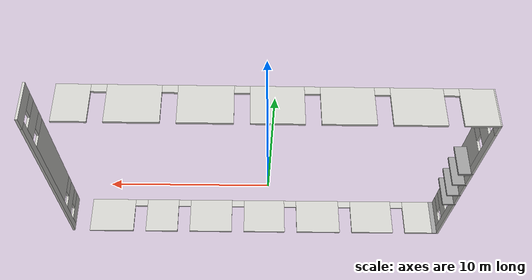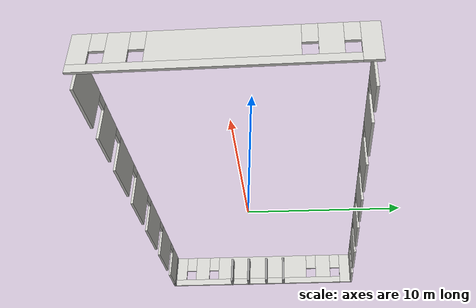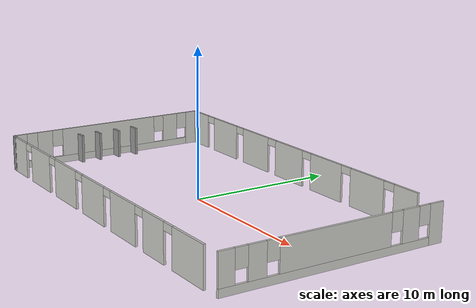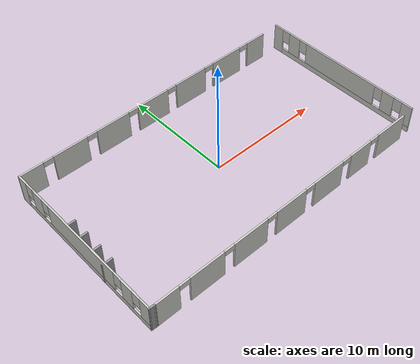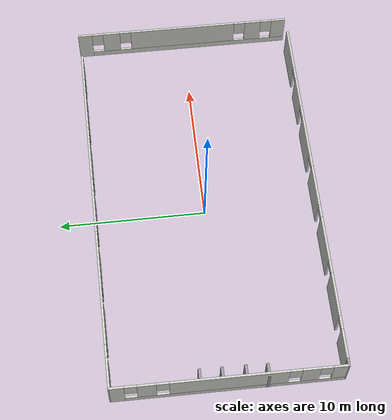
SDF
<?xml version='1.0'?>
<sdf version='1.6'>
  <model name='CV1_giardino2'>
    <link name='Door_1'>
      <pose frame=''>-12.2685 1.79069 0 0 -0 0</pose>
      <self_collide>0</self_collide>
      <kinematic>0</kinematic>
      <visual name='Door_1_Visual'>
        <pose frame=''>0 0 1 0 -0 0</pose>
        <geometry>
          <box>
            <size>0.9 0.17 2</size>
          </box>
        </geometry>
        <material>
          <script>
            <uri>file://media/materials/scripts/gazebo.material</uri>
            <name>Gazebo/Grey</name>
          </script>
          <ambient>0.3 0.3 0.3 1</ambient>
          <diffuse>0.7 0.7 0.7 1</diffuse>
          <specular>0.01 0.01 0.01 1</specular>
          <emissive>0 0 0 1</emissive>
        </material>
        <cast_shadows>1</cast_shadows>
        <transparency>0</transparency>
      </visual>
      <collision name='Door_1_Collision'>
        <laser_retro>0</laser_retro>
        <max_contacts>10</max_contacts>
        <pose frame=''>0 0 1 0 -0 0</pose>
        <geometry>
          <box>
            <size>0.9 0.17 2</size>
          </box>
        </geometry>
        <surface>
          <friction>
            <ode>
              <mu>1</mu>
              <mu2>1</mu2>
              <fdir1>0 0 0</fdir1>
              <slip1>0</slip1>
              <slip2>0</slip2>
            </ode>
            <torsional>
              <coefficient>1</coefficient>
              <patch_radius>0</patch_radius>
              <surface_radius>0</surface_radius>
              <use_patch_radius>1</use_patch_radius>
              <ode>
                <slip>0</slip>
              </ode>
            </torsional>
          </friction>
          <bounce>
            <restitution_coefficient>0</restitution_coefficient>
            <threshold>1e+06</threshold>
          </bounce>
          <contact>
            <collide_without_contact>0</collide_without_contact>
            <collide_without_contact_bitmask>1</collide_without_contact_bitmask>
            <collide_bitmask>1</collide_bitmask>
            <ode>
              <soft_cfm>0</soft_cfm>
              <soft_erp>0.2</soft_erp>
              <kp>1e+13</kp>
              <kd>1</kd>
              <max_vel>0.01</max_vel>
              <min_depth>0</min_depth>
            </ode>
            <bullet>
              <split_impulse>1</split_impulse>
              <split_impulse_penetration_threshold>-0.01</split_impulse_penetration_threshold>
              <soft_cfm>0</soft_cfm>
              <soft_erp>0.2</soft_erp>
              <kp>1e+13</kp>
              <kd>1</kd>
            </bullet>
          </contact>
        </surface>
      </collision>
    </link>
    <link name='Door_2'>
      <pose frame=''>-12.2685 0.359125 0 0 -0 0</pose>
      <self_collide>0</self_collide>
      <kinematic>0</kinematic>
      <visual name='Door_2_Visual'>
        <pose frame=''>0 0 1 0 -0 0</pose>
        <geometry>
          <box>
            <size>0.9 0.17 2</size>
          </box>
        </geometry>
        <material>
          <script>
            <uri>file://media/materials/scripts/gazebo.material</uri>
            <name>Gazebo/Grey</name>
          </script>
          <ambient>0.3 0.3 0.3 1</ambient>
          <diffuse>0.7 0.7 0.7 1</diffuse>
          <specular>0.01 0.01 0.01 1</specular>
          <emissive>0 0 0 1</emissive>
        </material>
        <cast_shadows>1</cast_shadows>
        <transparency>0</transparency>
      </visual>
      <collision name='Door_2_Collision'>
        <laser_retro>0</laser_retro>
        <max_contacts>10</max_contacts>
        <pose frame=''>0 0 1 0 -0 0</pose>
        <geometry>
          <box>
            <size>0.9 0.17 2</size>
          </box>
        </geometry>
        <surface>
          <friction>
            <ode>
              <mu>1</mu>
              <mu2>1</mu2>
              <fdir1>0 0 0</fdir1>
              <slip1>0</slip1>
              <slip2>0</slip2>
            </ode>
            <torsional>
              <coefficient>1</coefficient>
              <patch_radius>0</patch_radius>
              <surface_radius>0</surface_radius>
              <use_patch_radius>1</use_patch_radius>
              <ode>
                <slip>0</slip>
              </ode>
            </torsional>
          </friction>
          <bounce>
            <restitution_coefficient>0</restitution_coefficient>
            <threshold>1e+06</threshold>
          </bounce>
          <contact>
            <collide_without_contact>0</collide_without_contact>
            <collide_without_contact_bitmask>1</collide_without_contact_bitmask>
            <collide_bitmask>1</collide_bitmask>
            <ode>
              <soft_cfm>0</soft_cfm>
              <soft_erp>0.2</soft_erp>
              <kp>1e+13</kp>
              <kd>1</kd>
              <max_vel>0.01</max_vel>
              <min_depth>0</min_depth>
            </ode>
            <bullet>
              <split_impulse>1</split_impulse>
              <split_impulse_penetration_threshold>-0.01</split_impulse_penetration_threshold>
              <soft_cfm>0</soft_cfm>
              <soft_erp>0.2</soft_erp>
              <kp>1e+13</kp>
              <kd>1</kd>
            </bullet>
          </contact>
        </surface>
      </collision>
    </link>
    <link name='Door_3'>
      <pose frame=''>-12.296 -1.14905 0 0 -0 0</pose>
      <self_collide>0</self_collide>
      <kinematic>0</kinematic>
      <visual name='Door_3_Visual'>
        <pose frame=''>0 0 1 0 -0 0</pose>
        <geometry>
          <box>
            <size>0.9 0.17 2</size>
          </box>
        </geometry>
        <material>
          <script>
            <uri>file://media/materials/scripts/gazebo.material</uri>
            <name>Gazebo/Grey</name>
          </script>
          <ambient>0.3 0.3 0.3 1</ambient>
          <diffuse>0.7 0.7 0.7 1</diffuse>
          <specular>0.01 0.01 0.01 1</specular>
          <emissive>0 0 0 1</emissive>
        </material>
        <cast_shadows>1</cast_shadows>
        <transparency>0</transparency>
      </visual>
      <collision name='Door_3_Collision'>
        <laser_retro>0</laser_retro>
        <max_contacts>10</max_contacts>
        <pose frame=''>0 0 1 0 -0 0</pose>
        <geometry>
          <box>
            <size>0.9 0.17 2</size>
          </box>
        </geometry>
        <surface>
          <friction>
            <ode>
              <mu>1</mu>
              <mu2>1</mu2>
              <fdir1>0 0 0</fdir1>
              <slip1>0</slip1>
              <slip2>0</slip2>
            </ode>
            <torsional>
              <coefficient>1</coefficient>
              <patch_radius>0</patch_radius>
              <surface_radius>0</surface_radius>
              <use_patch_radius>1</use_patch_radius>
              <ode>
                <slip>0</slip>
              </ode>
            </torsional>
          </friction>
          <bounce>
            <restitution_coefficient>0</restitution_coefficient>
            <threshold>1e+06</threshold>
          </bounce>
          <contact>
            <collide_without_contact>0</collide_without_contact>
            <collide_without_contact_bitmask>1</collide_without_contact_bitmask>
            <collide_bitmask>1</collide_bitmask>
            <ode>
              <soft_cfm>0</soft_cfm>
              <soft_erp>0.2</soft_erp>
              <kp>1e+13</kp>
              <kd>1</kd>
              <max_vel>0.01</max_vel>
              <min_depth>0</min_depth>
            </ode>
            <bullet>
              <split_impulse>1</split_impulse>
              <split_impulse_penetration_threshold>-0.01</split_impulse_penetration_threshold>
              <soft_cfm>0</soft_cfm>
              <soft_erp>0.2</soft_erp>
              <kp>1e+13</kp>
              <kd>1</kd>
            </bullet>
          </contact>
        </surface>
      </collision>
    </link>
    <link name='Door_4'>
      <pose frame=''>-12.3517 -2.54114 0 0 -0 0</pose>
      <self_collide>0</self_collide>
      <kinematic>0</kinematic>
      <visual name='Door_4_Visual'>
        <pose frame=''>0 0 1 0 -0 0</pose>
        <geometry>
          <box>
            <size>0.9 0.17 2</size>
          </box>
        </geometry>
        <material>
          <script>
            <uri>file://media/materials/scripts/gazebo.material</uri>
            <name>Gazebo/Grey</name>
          </script>
          <ambient>0.3 0.3 0.3 1</ambient>
          <diffuse>0.7 0.7 0.7 1</diffuse>
          <specular>0.01 0.01 0.01 1</specular>
          <emissive>0 0 0 1</emissive>
        </material>
        <cast_shadows>1</cast_shadows>
        <transparency>0</transparency>
      </visual>
      <collision name='Door_4_Collision'>
        <laser_retro>0</laser_retro>
        <max_contacts>10</max_contacts>
        <pose frame=''>0 0 1 0 -0 0</pose>
        <geometry>
          <box>
            <size>0.9 0.17 2</size>
          </box>
        </geometry>
        <surface>
          <friction>
            <ode>
              <mu>1</mu>
              <mu2>1</mu2>
              <fdir1>0 0 0</fdir1>
              <slip1>0</slip1>
              <slip2>0</slip2>
            </ode>
            <torsional>
              <coefficient>1</coefficient>
              <patch_radius>0</patch_radius>
              <surface_radius>0</surface_radius>
              <use_patch_radius>1</use_patch_radius>
              <ode>
                <slip>0</slip>
              </ode>
            </torsional>
          </friction>
          <bounce>
            <restitution_coefficient>0</restitution_coefficient>
            <threshold>1e+06</threshold>
          </bounce>
          <contact>
            <collide_without_contact>0</collide_without_contact>
            <collide_without_contact_bitmask>1</collide_without_contact_bitmask>
            <collide_bitmask>1</collide_bitmask>
            <ode>
              <soft_cfm>0</soft_cfm>
              <soft_erp>0.2</soft_erp>
              <kp>1e+13</kp>
              <kd>1</kd>
              <max_vel>0.01</max_vel>
              <min_depth>0</min_depth>
            </ode>
            <bullet>
              <split_impulse>1</split_impulse>
              <split_impulse_penetration_threshold>-0.01</split_impulse_penetration_threshold>
              <soft_cfm>0</soft_cfm>
              <soft_erp>0.2</soft_erp>
              <kp>1e+13</kp>
              <kd>1</kd>
            </bullet>
          </contact>
        </surface>
      </collision>
    </link>
    <link name='Wall_0'>
      <pose frame=''>-12.7005 0.009036 0 0 0 -1.57729</pose>
      <self_collide>0</self_collide>
      <kinematic>0</kinematic>
      <visual name='Wall_0_Visual_0'>
        <pose frame=''>-7.07005 0 1.25 0 -0 0</pose>
        <geometry>
          <box>
            <size>0.999785 0.15 2.5</size>
          </box>
        </geometry>
        <material>
          <script>
            <uri>file://media/materials/scripts/gazebo.material</uri>
            <name>Gazebo/CeilingTiled</name>
          </script>
          <ambient>1 1 1 1</ambient>
          <diffuse>1 1 1 1</diffuse>
          <specular>0 0 0 1</specular>
          <emissive>0 0 0 1</emissive>
        </material>
        <cast_shadows>1</cast_shadows>
        <transparency>0</transparency>
      </visual>
      <visual name='Wall_0_Visual_1'>
        <pose frame=''>0.499892 0 0.25 0 -0 0</pose>
        <geometry>
          <box>
            <size>14.1401 0.15 0.5</size>
          </box>
        </geometry>
        <material>
          <script>
            <uri>file://media/materials/scripts/gazebo.material</uri>
            <name>Gazebo/CeilingTiled</name>
          </script>
          <ambient>1 1 1 1</ambient>
          <diffuse>1 1 1 1</diffuse>
          <specular>0 0 0 1</specular>
          <emissive>0 0 0 1</emissive>
        </material>
        <cast_shadows>1</cast_shadows>
        <transparency>0</transparency>
      </visual>
      <visual name='Wall_0_Visual_2'>
        <pose frame=''>-5.15824 0 1.5 0 -0 0</pose>
        <geometry>
          <box>
            <size>1.22384 0.15 2</size>
          </box>
        </geometry>
        <material>
          <script>
            <uri>file://media/materials/scripts/gazebo.material</uri>
            <name>Gazebo/CeilingTiled</name>
          </script>
          <ambient>1 1 1 1</ambient>
          <diffuse>1 1 1 1</diffuse>
          <specular>0 0 0 1</specular>
          <emissive>0 0 0 1</emissive>
        </material>
        <cast_shadows>1</cast_shadows>
        <transparency>0</transparency>
      </visual>
      <visual name='Wall_0_Visual_3'>
        <pose frame=''>0.034926 0 1.5 0 -0 0</pose>
        <geometry>
          <box>
            <size>7.56249 0.15 2</size>
          </box>
        </geometry>
        <material>
          <script>
            <uri>file://media/materials/scripts/gazebo.material</uri>
            <name>Gazebo/CeilingTiled</name>
          </script>
          <ambient>1 1 1 1</ambient>
          <diffuse>1 1 1 1</diffuse>
          <specular>0 0 0 1</specular>
          <emissive>0 0 0 1</emissive>
        </material>
        <cast_shadows>1</cast_shadows>
        <transparency>0</transparency>
      </visual>
      <visual name='Wall_0_Visual_4'>
        <pose frame=''>5.1919 0 1.5 0 -0 0</pose>
        <geometry>
          <box>
            <size>1.15146 0.15 2</size>
          </box>
        </geometry>
        <material>
          <script>
            <uri>file://media/materials/scripts/gazebo.material</uri>
            <name>Gazebo/CeilingTiled</name>
          </script>
          <ambient>1 1 1 1</ambient>
          <diffuse>1 1 1 1</diffuse>
          <specular>0 0 0 1</specular>
          <emissive>0 0 0 1</emissive>
        </material>
        <cast_shadows>1</cast_shadows>
        <transparency>0</transparency>
      </visual>
      <visual name='Wall_0_Visual_5'>
        <pose frame=''>7.06879 0 1.5 0 -0 0</pose>
        <geometry>
          <box>
            <size>1.00231 0.15 2</size>
          </box>
        </geometry>
        <material>
          <script>
            <uri>file://media/materials/scripts/gazebo.material</uri>
            <name>Gazebo/CeilingTiled</name>
          </script>
          <ambient>1 1 1 1</ambient>
          <diffuse>1 1 1 1</diffuse>
          <specular>0 0 0 1</specular>
          <emissive>0 0 0 1</emissive>
        </material>
        <cast_shadows>1</cast_shadows>
        <transparency>0</transparency>
      </visual>
      <visual name='Wall_0_Visual_6'>
        <pose frame=''>-6.17016 0 1.9 0 -0 0</pose>
        <geometry>
          <box>
            <size>0.8 0.15 1.2</size>
          </box>
        </geometry>
        <material>
          <script>
            <uri>file://media/materials/scripts/gazebo.material</uri>
            <name>Gazebo/CeilingTiled</name>
          </script>
          <ambient>1 1 1 1</ambient>
          <diffuse>1 1 1 1</diffuse>
          <specular>0 0 0 1</specular>
          <emissive>0 0 0 1</emissive>
        </material>
        <cast_shadows>1</cast_shadows>
        <transparency>0</transparency>
      </visual>
      <visual name='Wall_0_Visual_7'>
        <pose frame=''>-4.14632 0 1.9 0 -0 0</pose>
        <geometry>
          <box>
            <size>0.8 0.15 1.2</size>
          </box>
        </geometry>
        <material>
          <script>
            <uri>file://media/materials/scripts/gazebo.material</uri>
            <name>Gazebo/CeilingTiled</name>
          </script>
          <ambient>1 1 1 1</ambient>
          <diffuse>1 1 1 1</diffuse>
          <specular>0 0 0 1</specular>
          <emissive>0 0 0 1</emissive>
        </material>
        <cast_shadows>1</cast_shadows>
        <transparency>0</transparency>
      </visual>
      <visual name='Wall_0_Visual_8'>
        <pose frame=''>4.21617 0 1.9 0 -0 0</pose>
        <geometry>
          <box>
            <size>0.8 0.15 1.2</size>
          </box>
        </geometry>
        <material>
          <script>
            <uri>file://media/materials/scripts/gazebo.material</uri>
            <name>Gazebo/CeilingTiled</name>
          </script>
          <ambient>1 1 1 1</ambient>
          <diffuse>1 1 1 1</diffuse>
          <specular>0 0 0 1</specular>
          <emissive>0 0 0 1</emissive>
        </material>
        <cast_shadows>1</cast_shadows>
        <transparency>0</transparency>
      </visual>
      <visual name='Wall_0_Visual_9'>
        <pose frame=''>6.16763 0 1.9 0 -0 0</pose>
        <geometry>
          <box>
            <size>0.8 0.15 1.2</size>
          </box>
        </geometry>
        <material>
          <script>
            <uri>file://media/materials/scripts/gazebo.material</uri>
            <name>Gazebo/CeilingTiled</name>
          </script>
          <ambient>1 1 1 1</ambient>
          <diffuse>1 1 1 1</diffuse>
          <specular>0 0 0 1</specular>
          <emissive>0 0 0 1</emissive>
        </material>
        <cast_shadows>1</cast_shadows>
        <transparency>0</transparency>
      </visual>
      <collision name='Wall_0_Collision_0'>
        <laser_retro>0</laser_retro>
        <max_contacts>10</max_contacts>
        <pose frame=''>-7.07005 0 1.25 0 -0 0</pose>
        <geometry>
          <box>
            <size>0.999785 0.15 2.5</size>
          </box>
        </geometry>
        <surface>
          <friction>
            <ode>
              <mu>1</mu>
              <mu2>1</mu2>
              <fdir1>0 0 0</fdir1>
              <slip1>0</slip1>
              <slip2>0</slip2>
            </ode>
            <torsional>
              <coefficient>1</coefficient>
              <patch_radius>0</patch_radius>
              <surface_radius>0</surface_radius>
              <use_patch_radius>1</use_patch_radius>
              <ode>
                <slip>0</slip>
              </ode>
            </torsional>
          </friction>
          <bounce>
            <restitution_coefficient>0</restitution_coefficient>
            <threshold>1e+06</threshold>
          </bounce>
          <contact>
            <collide_without_contact>0</collide_without_contact>
            <collide_without_contact_bitmask>1</collide_without_contact_bitmask>
            <collide_bitmask>1</collide_bitmask>
            <ode>
              <soft_cfm>0</soft_cfm>
              <soft_erp>0.2</soft_erp>
              <kp>1e+13</kp>
              <kd>1</kd>
              <max_vel>0.01</max_vel>
              <min_depth>0</min_depth>
            </ode>
            <bullet>
              <split_impulse>1</split_impulse>
              <split_impulse_penetration_threshold>-0.01</split_impulse_penetration_threshold>
              <soft_cfm>0</soft_cfm>
              <soft_erp>0.2</soft_erp>
              <kp>1e+13</kp>
              <kd>1</kd>
            </bullet>
          </contact>
        </surface>
      </collision>
      <collision name='Wall_0_Collision_1'>
        <laser_retro>0</laser_retro>
        <max_contacts>10</max_contacts>
        <pose frame=''>0.499892 0 0.25 0 -0 0</pose>
        <geometry>
          <box>
            <size>14.1401 0.15 0.5</size>
          </box>
        </geometry>
        <surface>
          <friction>
            <ode>
              <mu>1</mu>
              <mu2>1</mu2>
              <fdir1>0 0 0</fdir1>
              <slip1>0</slip1>
              <slip2>0</slip2>
            </ode>
            <torsional>
              <coefficient>1</coefficient>
              <patch_radius>0</patch_radius>
              <surface_radius>0</surface_radius>
              <use_patch_radius>1</use_patch_radius>
              <ode>
                <slip>0</slip>
              </ode>
            </torsional>
          </friction>
          <bounce>
            <restitution_coefficient>0</restitution_coefficient>
            <threshold>1e+06</threshold>
          </bounce>
          <contact>
            <collide_without_contact>0</collide_without_contact>
            <collide_without_contact_bitmask>1</collide_without_contact_bitmask>
            <collide_bitmask>1</collide_bitmask>
            <ode>
              <soft_cfm>0</soft_cfm>
              <soft_erp>0.2</soft_erp>
              <kp>1e+13</kp>
              <kd>1</kd>
              <max_vel>0.01</max_vel>
              <min_depth>0</min_depth>
            </ode>
            <bullet>
              <split_impulse>1</split_impulse>
              <split_impulse_penetration_threshold>-0.01</split_impulse_penetration_threshold>
              <soft_cfm>0</soft_cfm>
              <soft_erp>0.2</soft_erp>
              <kp>1e+13</kp>
              <kd>1</kd>
            </bullet>
          </contact>
        </surface>
      </collision>
      <collision name='Wall_0_Collision_2'>
        <laser_retro>0</laser_retro>
        <max_contacts>10</max_contacts>
        <pose frame=''>-5.15824 0 1.5 0 -0 0</pose>
        <geometry>
          <box>
            <size>1.22384 0.15 2</size>
          </box>
        </geometry>
        <surface>
          <friction>
            <ode>
              <mu>1</mu>
              <mu2>1</mu2>
              <fdir1>0 0 0</fdir1>
              <slip1>0</slip1>
              <slip2>0</slip2>
            </ode>
            <torsional>
              <coefficient>1</coefficient>
              <patch_radius>0</patch_radius>
              <surface_radius>0</surface_radius>
              <use_patch_radius>1</use_patch_radius>
              <ode>
                <slip>0</slip>
              </ode>
            </torsional>
          </friction>
          <bounce>
            <restitution_coefficient>0</restitution_coefficient>
            <threshold>1e+06</threshold>
          </bounce>
          <contact>
            <collide_without_contact>0</collide_without_contact>
            <collide_without_contact_bitmask>1</collide_without_contact_bitmask>
            <collide_bitmask>1</collide_bitmask>
            <ode>
              <soft_cfm>0</soft_cfm>
              <soft_erp>0.2</soft_erp>
              <kp>1e+13</kp>
              <kd>1</kd>
              <max_vel>0.01</max_vel>
              <min_depth>0</min_depth>
            </ode>
            <bullet>
              <split_impulse>1</split_impulse>
              <split_impulse_penetration_threshold>-0.01</split_impulse_penetration_threshold>
              <soft_cfm>0</soft_cfm>
              <soft_erp>0.2</soft_erp>
              <kp>1e+13</kp>
              <kd>1</kd>
            </bullet>
          </contact>
        </surface>
      </collision>
      <collision name='Wall_0_Collision_3'>
        <laser_retro>0</laser_retro>
        <max_contacts>10</max_contacts>
        <pose frame=''>0.034926 0 1.5 0 -0 0</pose>
        <geometry>
          <box>
            <size>7.56249 0.15 2</size>
          </box>
        </geometry>
        <surface>
          <friction>
            <ode>
              <mu>1</mu>
              <mu2>1</mu2>
              <fdir1>0 0 0</fdir1>
              <slip1>0</slip1>
              <slip2>0</slip2>
            </ode>
            <torsional>
              <coefficient>1</coefficient>
              <patch_radius>0</patch_radius>
              <surface_radius>0</surface_radius>
              <use_patch_radius>1</use_patch_radius>
              <ode>
                <slip>0</slip>
              </ode>
            </torsional>
          </friction>
          <bounce>
            <restitution_coefficient>0</restitution_coefficient>
            <threshold>1e+06</threshold>
          </bounce>
          <contact>
            <collide_without_contact>0</collide_without_contact>
            <collide_without_contact_bitmask>1</collide_without_contact_bitmask>
            <collide_bitmask>1</collide_bitmask>
            <ode>
              <soft_cfm>0</soft_cfm>
              <soft_erp>0.2</soft_erp>
              <kp>1e+13</kp>
              <kd>1</kd>
              <max_vel>0.01</max_vel>
              <min_depth>0</min_depth>
            </ode>
            <bullet>
              <split_impulse>1</split_impulse>
              <split_impulse_penetration_threshold>-0.01</split_impulse_penetration_threshold>
              <soft_cfm>0</soft_cfm>
              <soft_erp>0.2</soft_erp>
              <kp>1e+13</kp>
              <kd>1</kd>
            </bullet>
          </contact>
        </surface>
      </collision>
      <collision name='Wall_0_Collision_5'>
        <laser_retro>0</laser_retro>
        <max_contacts>10</max_contacts>
        <pose frame=''>7.06879 0 1.5 0 -0 0</pose>
        <geometry>
          <box>
            <size>1.00231 0.15 2</size>
          </box>
        </geometry>
        <surface>
          <friction>
            <ode>
              <mu>1</mu>
              <mu2>1</mu2>
              <fdir1>0 0 0</fdir1>
              <slip1>0</slip1>
              <slip2>0</slip2>
            </ode>
            <torsional>
              <coefficient>1</coefficient>
              <patch_radius>0</patch_radius>
              <surface_radius>0</surface_radius>
              <use_patch_radius>1</use_patch_radius>
              <ode>
                <slip>0</slip>
              </ode>
            </torsional>
          </friction>
          <bounce>
            <restitution_coefficient>0</restitution_coefficient>
            <threshold>1e+06</threshold>
          </bounce>
          <contact>
            <collide_without_contact>0</collide_without_contact>
            <collide_without_contact_bitmask>1</collide_without_contact_bitmask>
            <collide_bitmask>1</collide_bitmask>
            <ode>
              <soft_cfm>0</soft_cfm>
              <soft_erp>0.2</soft_erp>
              <kp>1e+13</kp>
              <kd>1</kd>
              <max_vel>0.01</max_vel>
              <min_depth>0</min_depth>
            </ode>
            <bullet>
              <split_impulse>1</split_impulse>
              <split_impulse_penetration_threshold>-0.01</split_impulse_penetration_threshold>
              <soft_cfm>0</soft_cfm>
              <soft_erp>0.2</soft_erp>
              <kp>1e+13</kp>
              <kd>1</kd>
            </bullet>
          </contact>
        </surface>
      </collision>
      <collision name='Wall_0_Collision_4'>
        <laser_retro>0</laser_retro>
        <max_contacts>10</max_contacts>
        <pose frame=''>5.1919 0 1.5 0 -0 0</pose>
        <geometry>
          <box>
            <size>1.15146 0.15 2</size>
          </box>
        </geometry>
        <surface>
          <friction>
            <ode>
              <mu>1</mu>
              <mu2>1</mu2>
              <fdir1>0 0 0</fdir1>
              <slip1>0</slip1>
              <slip2>0</slip2>
            </ode>
            <torsional>
              <coefficient>1</coefficient>
              <patch_radius>0</patch_radius>
              <surface_radius>0</surface_radius>
              <use_patch_radius>1</use_patch_radius>
              <ode>
                <slip>0</slip>
              </ode>
            </torsional>
          </friction>
          <bounce>
            <restitution_coefficient>0</restitution_coefficient>
            <threshold>1e+06</threshold>
          </bounce>
          <contact>
            <collide_without_contact>0</collide_without_contact>
            <collide_without_contact_bitmask>1</collide_without_contact_bitmask>
            <collide_bitmask>1</collide_bitmask>
            <ode>
              <soft_cfm>0</soft_cfm>
              <soft_erp>0.2</soft_erp>
              <kp>1e+13</kp>
              <kd>1</kd>
              <max_vel>0.01</max_vel>
              <min_depth>0</min_depth>
            </ode>
            <bullet>
              <split_impulse>1</split_impulse>
              <split_impulse_penetration_threshold>-0.01</split_impulse_penetration_threshold>
              <soft_cfm>0</soft_cfm>
              <soft_erp>0.2</soft_erp>
              <kp>1e+13</kp>
              <kd>1</kd>
            </bullet>
          </contact>
        </surface>
      </collision>
      <collision name='Wall_0_Collision_6'>
        <laser_retro>0</laser_retro>
        <max_contacts>10</max_contacts>
        <pose frame=''>-6.17016 0 1.9 0 -0 0</pose>
        <geometry>
          <box>
            <size>0.8 0.15 1.2</size>
          </box>
        </geometry>
        <surface>
          <friction>
            <ode>
              <mu>1</mu>
              <mu2>1</mu2>
              <fdir1>0 0 0</fdir1>
              <slip1>0</slip1>
              <slip2>0</slip2>
            </ode>
            <torsional>
              <coefficient>1</coefficient>
              <patch_radius>0</patch_radius>
              <surface_radius>0</surface_radius>
              <use_patch_radius>1</use_patch_radius>
              <ode>
                <slip>0</slip>
              </ode>
            </torsional>
          </friction>
          <bounce>
            <restitution_coefficient>0</restitution_coefficient>
            <threshold>1e+06</threshold>
          </bounce>
          <contact>
            <collide_without_contact>0</collide_without_contact>
            <collide_without_contact_bitmask>1</collide_without_contact_bitmask>
            <collide_bitmask>1</collide_bitmask>
            <ode>
              <soft_cfm>0</soft_cfm>
              <soft_erp>0.2</soft_erp>
              <kp>1e+13</kp>
              <kd>1</kd>
              <max_vel>0.01</max_vel>
              <min_depth>0</min_depth>
            </ode>
            <bullet>
              <split_impulse>1</split_impulse>
              <split_impulse_penetration_threshold>-0.01</split_impulse_penetration_threshold>
              <soft_cfm>0</soft_cfm>
              <soft_erp>0.2</soft_erp>
              <kp>1e+13</kp>
              <kd>1</kd>
            </bullet>
          </contact>
        </surface>
      </collision>
      <collision name='Wall_0_Collision_7'>
        <laser_retro>0</laser_retro>
        <max_contacts>10</max_contacts>
        <pose frame=''>-4.14632 0 1.9 0 -0 0</pose>
        <geometry>
          <box>
            <size>0.8 0.15 1.2</size>
          </box>
        </geometry>
        <surface>
          <friction>
            <ode>
              <mu>1</mu>
              <mu2>1</mu2>
              <fdir1>0 0 0</fdir1>
              <slip1>0</slip1>
              <slip2>0</slip2>
            </ode>
            <torsional>
              <coefficient>1</coefficient>
              <patch_radius>0</patch_radius>
              <surface_radius>0</surface_radius>
              <use_patch_radius>1</use_patch_radius>
              <ode>
                <slip>0</slip>
              </ode>
            </torsional>
          </friction>
          <bounce>
            <restitution_coefficient>0</restitution_coefficient>
            <threshold>1e+06</threshold>
          </bounce>
          <contact>
            <collide_without_contact>0</collide_without_contact>
            <collide_without_contact_bitmask>1</collide_without_contact_bitmask>
            <collide_bitmask>1</collide_bitmask>
            <ode>
              <soft_cfm>0</soft_cfm>
              <soft_erp>0.2</soft_erp>
              <kp>1e+13</kp>
              <kd>1</kd>
              <max_vel>0.01</max_vel>
              <min_depth>0</min_depth>
            </ode>
            <bullet>
              <split_impulse>1</split_impulse>
              <split_impulse_penetration_threshold>-0.01</split_impulse_penetration_threshold>
              <soft_cfm>0</soft_cfm>
              <soft_erp>0.2</soft_erp>
              <kp>1e+13</kp>
              <kd>1</kd>
            </bullet>
          </contact>
        </surface>
      </collision>
      <collision name='Wall_0_Collision_9'>
        <laser_retro>0</laser_retro>
        <max_contacts>10</max_contacts>
        <pose frame=''>6.16763 0 1.9 0 -0 0</pose>
        <geometry>
          <box>
            <size>0.8 0.15 1.2</size>
          </box>
        </geometry>
        <surface>
          <friction>
            <ode>
              <mu>1</mu>
              <mu2>1</mu2>
              <fdir1>0 0 0</fdir1>
              <slip1>0</slip1>
              <slip2>0</slip2>
            </ode>
            <torsional>
              <coefficient>1</coefficient>
              <patch_radius>0</patch_radius>
              <surface_radius>0</surface_radius>
              <use_patch_radius>1</use_patch_radius>
              <ode>
                <slip>0</slip>
              </ode>
            </torsional>
          </friction>
          <bounce>
            <restitution_coefficient>0</restitution_coefficient>
            <threshold>1e+06</threshold>
          </bounce>
          <contact>
            <collide_without_contact>0</collide_without_contact>
            <collide_without_contact_bitmask>1</collide_without_contact_bitmask>
            <collide_bitmask>1</collide_bitmask>
            <ode>
              <soft_cfm>0</soft_cfm>
              <soft_erp>0.2</soft_erp>
              <kp>1e+13</kp>
              <kd>1</kd>
              <max_vel>0.01</max_vel>
              <min_depth>0</min_depth>
            </ode>
            <bullet>
              <split_impulse>1</split_impulse>
              <split_impulse_penetration_threshold>-0.01</split_impulse_penetration_threshold>
              <soft_cfm>0</soft_cfm>
              <soft_erp>0.2</soft_erp>
              <kp>1e+13</kp>
              <kd>1</kd>
            </bullet>
          </contact>
        </surface>
      </collision>
      <collision name='Wall_0_Collision_8'>
        <laser_retro>0</laser_retro>
        <max_contacts>10</max_contacts>
        <pose frame=''>4.21617 0 1.9 0 -0 0</pose>
        <geometry>
          <box>
            <size>0.8 0.15 1.2</size>
          </box>
        </geometry>
        <surface>
          <friction>
            <ode>
              <mu>1</mu>
              <mu2>1</mu2>
              <fdir1>0 0 0</fdir1>
              <slip1>0</slip1>
              <slip2>0</slip2>
            </ode>
            <torsional>
              <coefficient>1</coefficient>
              <patch_radius>0</patch_radius>
              <surface_radius>0</surface_radius>
              <use_patch_radius>1</use_patch_radius>
              <ode>
                <slip>0</slip>
              </ode>
            </torsional>
          </friction>
          <bounce>
            <restitution_coefficient>0</restitution_coefficient>
            <threshold>1e+06</threshold>
          </bounce>
          <contact>
            <collide_without_contact>0</collide_without_contact>
            <collide_without_contact_bitmask>1</collide_without_contact_bitmask>
            <collide_bitmask>1</collide_bitmask>
            <ode>
              <soft_cfm>0</soft_cfm>
              <soft_erp>0.2</soft_erp>
              <kp>1e+13</kp>
              <kd>1</kd>
              <max_vel>0.01</max_vel>
              <min_depth>0</min_depth>
            </ode>
            <bullet>
              <split_impulse>1</split_impulse>
              <split_impulse_penetration_threshold>-0.01</split_impulse_penetration_threshold>
              <soft_cfm>0</soft_cfm>
              <soft_erp>0.2</soft_erp>
              <kp>1e+13</kp>
              <kd>1</kd>
            </bullet>
          </contact>
        </surface>
      </collision>
    </link>
    <link name='Wall_0_clone'>
      <pose frame=''>14.0185 0.09324 0 0 0 -1.57729</pose>
      <self_collide>0</self_collide>
      <kinematic>0</kinematic>
      <visual name='Wall_0_Visual_4'>
        <pose frame=''>5.1919 0 1.5 0 -0 0</pose>
        <geometry>
          <box>
            <size>1.15146 0.15 2</size>
          </box>
        </geometry>
        <material>
          <script>
            <uri>file://media/materials/scripts/gazebo.material</uri>
            <name>Gazebo/CeilingTiled</name>
          </script>
          <ambient>1 1 1 1</ambient>
          <diffuse>1 1 1 1</diffuse>
          <specular>0 0 0 1</specular>
          <emissive>0 0 0 1</emissive>
          <shader type='pixel'/>
        </material>
        <cast_shadows>1</cast_shadows>
        <transparency>0</transparency>
      </visual>
      <visual name='Wall_0_Visual_1'>
        <pose frame=''>0.499892 0 0.25 0 -0 0</pose>
        <geometry>
          <box>
            <size>14.1401 0.15 0.5</size>
          </box>
        </geometry>
        <material>
          <script>
            <uri>file://media/materials/scripts/gazebo.material</uri>
            <name>Gazebo/CeilingTiled</name>
          </script>
          <ambient>1 1 1 1</ambient>
          <diffuse>1 1 1 1</diffuse>
          <specular>0 0 0 1</specular>
          <emissive>0 0 0 1</emissive>
          <shader type='pixel'/>
        </material>
        <cast_shadows>1</cast_shadows>
        <transparency>0</transparency>
      </visual>
      <visual name='Wall_0_Visual_0'>
        <pose frame=''>-7.07005 0 1.25 0 -0 0</pose>
        <geometry>
          <box>
            <size>0.999785 0.15 2.5</size>
          </box>
        </geometry>
        <material>
          <script>
            <uri>file://media/materials/scripts/gazebo.material</uri>
            <name>Gazebo/CeilingTiled</name>
          </script>
          <ambient>1 1 1 1</ambient>
          <diffuse>1 1 1 1</diffuse>
          <specular>0 0 0 1</specular>
          <emissive>0 0 0 1</emissive>
          <shader type='pixel'/>
        </material>
        <cast_shadows>1</cast_shadows>
        <transparency>0</transparency>
      </visual>
      <visual name='Wall_0_Visual_2'>
        <pose frame=''>-5.15824 0 1.5 0 -0 0</pose>
        <geometry>
          <box>
            <size>1.22384 0.15 2</size>
          </box>
        </geometry>
        <material>
          <script>
            <uri>file://media/materials/scripts/gazebo.material</uri>
            <name>Gazebo/CeilingTiled</name>
          </script>
          <ambient>1 1 1 1</ambient>
          <diffuse>1 1 1 1</diffuse>
          <specular>0 0 0 1</specular>
          <emissive>0 0 0 1</emissive>
          <shader type='pixel'/>
        </material>
        <cast_shadows>1</cast_shadows>
        <transparency>0</transparency>
      </visual>
      <visual name='Wall_0_Visual_3'>
        <pose frame=''>0.034926 0 1.5 0 -0 0</pose>
        <geometry>
          <box>
            <size>7.56249 0.15 2</size>
          </box>
        </geometry>
        <material>
          <script>
            <uri>file://media/materials/scripts/gazebo.material</uri>
            <name>Gazebo/CeilingTiled</name>
          </script>
          <ambient>1 1 1 1</ambient>
          <diffuse>1 1 1 1</diffuse>
          <specular>0 0 0 1</specular>
          <emissive>0 0 0 1</emissive>
          <shader type='pixel'/>
        </material>
        <cast_shadows>1</cast_shadows>
        <transparency>0</transparency>
      </visual>
      <visual name='Wall_0_Visual_5'>
        <pose frame=''>7.06879 0 1.5 0 -0 0</pose>
        <geometry>
          <box>
            <size>1.00231 0.15 2</size>
          </box>
        </geometry>
        <material>
          <script>
            <uri>file://media/materials/scripts/gazebo.material</uri>
            <name>Gazebo/CeilingTiled</name>
          </script>
          <ambient>1 1 1 1</ambient>
          <diffuse>1 1 1 1</diffuse>
          <specular>0 0 0 1</specular>
          <emissive>0 0 0 1</emissive>
          <shader type='pixel'/>
        </material>
        <cast_shadows>1</cast_shadows>
        <transparency>0</transparency>
      </visual>
      <visual name='Wall_0_Visual_6'>
        <pose frame=''>-6.17016 0 1.9 0 -0 0</pose>
        <geometry>
          <box>
            <size>0.8 0.15 1.2</size>
          </box>
        </geometry>
        <material>
          <script>
            <uri>file://media/materials/scripts/gazebo.material</uri>
            <name>Gazebo/CeilingTiled</name>
          </script>
          <ambient>1 1 1 1</ambient>
          <diffuse>1 1 1 1</diffuse>
          <specular>0 0 0 1</specular>
          <emissive>0 0 0 1</emissive>
          <shader type='pixel'/>
        </material>
        <cast_shadows>1</cast_shadows>
        <transparency>0</transparency>
      </visual>
      <visual name='Wall_0_Visual_7'>
        <pose frame=''>-4.14632 0 1.9 0 -0 0</pose>
        <geometry>
          <box>
            <size>0.8 0.15 1.2</size>
          </box>
        </geometry>
        <material>
          <script>
            <uri>file://media/materials/scripts/gazebo.material</uri>
            <name>Gazebo/CeilingTiled</name>
          </script>
          <ambient>1 1 1 1</ambient>
          <diffuse>1 1 1 1</diffuse>
          <specular>0 0 0 1</specular>
          <emissive>0 0 0 1</emissive>
          <shader type='pixel'/>
        </material>
        <cast_shadows>1</cast_shadows>
        <transparency>0</transparency>
      </visual>
      <visual name='Wall_0_Visual_8'>
        <pose frame=''>4.21617 0 1.9 0 -0 0</pose>
        <geometry>
          <box>
            <size>0.8 0.15 1.2</size>
          </box>
        </geometry>
        <material>
          <script>
            <uri>file://media/materials/scripts/gazebo.material</uri>
            <name>Gazebo/CeilingTiled</name>
          </script>
          <ambient>1 1 1 1</ambient>
          <diffuse>1 1 1 1</diffuse>
          <specular>0 0 0 1</specular>
          <emissive>0 0 0 1</emissive>
          <shader type='pixel'/>
        </material>
        <cast_shadows>1</cast_shadows>
        <transparency>0</transparency>
      </visual>
      <visual name='Wall_0_Visual_9'>
        <pose frame=''>6.16763 0 1.9 0 -0 0</pose>
        <geometry>
          <box>
            <size>0.8 0.15 1.2</size>
          </box>
        </geometry>
        <material>
          <script>
            <uri>file://media/materials/scripts/gazebo.material</uri>
            <name>Gazebo/CeilingTiled</name>
          </script>
          <ambient>1 1 1 1</ambient>
          <diffuse>1 1 1 1</diffuse>
          <specular>0 0 0 1</specular>
          <emissive>0 0 0 1</emissive>
          <shader type='pixel'/>
        </material>
        <cast_shadows>1</cast_shadows>
        <transparency>0</transparency>
      </visual>
      <collision name='Wall_0_Collision_0'>
        <laser_retro>0</laser_retro>
        <max_contacts>10</max_contacts>
        <pose frame=''>-7.07005 0 1.25 0 -0 0</pose>
        <geometry>
          <box>
            <size>0.999785 0.15 2.5</size>
          </box>
        </geometry>
        <surface>
          <friction>
            <ode>
              <mu>1</mu>
              <mu2>1</mu2>
              <fdir1>0 0 0</fdir1>
              <slip1>0</slip1>
              <slip2>0</slip2>
            </ode>
            <torsional>
              <coefficient>1</coefficient>
              <patch_radius>0</patch_radius>
              <surface_radius>0</surface_radius>
              <use_patch_radius>1</use_patch_radius>
              <ode>
                <slip>0</slip>
              </ode>
            </torsional>
          </friction>
          <bounce>
            <restitution_coefficient>0</restitution_coefficient>
            <threshold>1e+06</threshold>
          </bounce>
          <contact>
            <collide_without_contact>0</collide_without_contact>
            <collide_without_contact_bitmask>1</collide_without_contact_bitmask>
            <collide_bitmask>1</collide_bitmask>
            <ode>
              <soft_cfm>0</soft_cfm>
              <soft_erp>0.2</soft_erp>
              <kp>1e+13</kp>
              <kd>1</kd>
              <max_vel>0.01</max_vel>
              <min_depth>0</min_depth>
            </ode>
            <bullet>
              <split_impulse>1</split_impulse>
              <split_impulse_penetration_threshold>-0.01</split_impulse_penetration_threshold>
              <soft_cfm>0</soft_cfm>
              <soft_erp>0.2</soft_erp>
              <kp>1e+13</kp>
              <kd>1</kd>
            </bullet>
          </contact>
        </surface>
      </collision>
      <collision name='Wall_0_Collision_1'>
        <laser_retro>0</laser_retro>
        <max_contacts>10</max_contacts>
        <pose frame=''>0.499892 0 0.25 0 -0 0</pose>
        <geometry>
          <box>
            <size>14.1401 0.15 0.5</size>
          </box>
        </geometry>
        <surface>
          <friction>
            <ode>
              <mu>1</mu>
              <mu2>1</mu2>
              <fdir1>0 0 0</fdir1>
              <slip1>0</slip1>
              <slip2>0</slip2>
            </ode>
            <torsional>
              <coefficient>1</coefficient>
              <patch_radius>0</patch_radius>
              <surface_radius>0</surface_radius>
              <use_patch_radius>1</use_patch_radius>
              <ode>
                <slip>0</slip>
              </ode>
            </torsional>
          </friction>
          <bounce>
            <restitution_coefficient>0</restitution_coefficient>
            <threshold>1e+06</threshold>
          </bounce>
          <contact>
            <collide_without_contact>0</collide_without_contact>
            <collide_without_contact_bitmask>1</collide_without_contact_bitmask>
            <collide_bitmask>1</collide_bitmask>
            <ode>
              <soft_cfm>0</soft_cfm>
              <soft_erp>0.2</soft_erp>
              <kp>1e+13</kp>
              <kd>1</kd>
              <max_vel>0.01</max_vel>
              <min_depth>0</min_depth>
            </ode>
            <bullet>
              <split_impulse>1</split_impulse>
              <split_impulse_penetration_threshold>-0.01</split_impulse_penetration_threshold>
              <soft_cfm>0</soft_cfm>
              <soft_erp>0.2</soft_erp>
              <kp>1e+13</kp>
              <kd>1</kd>
            </bullet>
          </contact>
        </surface>
      </collision>
      <collision name='Wall_0_Collision_2'>
        <laser_retro>0</laser_retro>
        <max_contacts>10</max_contacts>
        <pose frame=''>-5.15824 0 1.5 0 -0 0</pose>
        <geometry>
          <box>
            <size>1.22384 0.15 2</size>
          </box>
        </geometry>
        <surface>
          <friction>
            <ode>
              <mu>1</mu>
              <mu2>1</mu2>
              <fdir1>0 0 0</fdir1>
              <slip1>0</slip1>
              <slip2>0</slip2>
            </ode>
            <torsional>
              <coefficient>1</coefficient>
              <patch_radius>0</patch_radius>
              <surface_radius>0</surface_radius>
              <use_patch_radius>1</use_patch_radius>
              <ode>
                <slip>0</slip>
              </ode>
            </torsional>
          </friction>
          <bounce>
            <restitution_coefficient>0</restitution_coefficient>
            <threshold>1e+06</threshold>
          </bounce>
          <contact>
            <collide_without_contact>0</collide_without_contact>
            <collide_without_contact_bitmask>1</collide_without_contact_bitmask>
            <collide_bitmask>1</collide_bitmask>
            <ode>
              <soft_cfm>0</soft_cfm>
              <soft_erp>0.2</soft_erp>
              <kp>1e+13</kp>
              <kd>1</kd>
              <max_vel>0.01</max_vel>
              <min_depth>0</min_depth>
            </ode>
            <bullet>
              <split_impulse>1</split_impulse>
              <split_impulse_penetration_threshold>-0.01</split_impulse_penetration_threshold>
              <soft_cfm>0</soft_cfm>
              <soft_erp>0.2</soft_erp>
              <kp>1e+13</kp>
              <kd>1</kd>
            </bullet>
          </contact>
        </surface>
      </collision>
      <collision name='Wall_0_Collision_3'>
        <laser_retro>0</laser_retro>
        <max_contacts>10</max_contacts>
        <pose frame=''>0.034926 0 1.5 0 -0 0</pose>
        <geometry>
          <box>
            <size>7.56249 0.15 2</size>
          </box>
        </geometry>
        <surface>
          <friction>
            <ode>
              <mu>1</mu>
              <mu2>1</mu2>
              <fdir1>0 0 0</fdir1>
              <slip1>0</slip1>
              <slip2>0</slip2>
            </ode>
            <torsional>
              <coefficient>1</coefficient>
              <patch_radius>0</patch_radius>
              <surface_radius>0</surface_radius>
              <use_patch_radius>1</use_patch_radius>
              <ode>
                <slip>0</slip>
              </ode>
            </torsional>
          </friction>
          <bounce>
            <restitution_coefficient>0</restitution_coefficient>
            <threshold>1e+06</threshold>
          </bounce>
          <contact>
            <collide_without_contact>0</collide_without_contact>
            <collide_without_contact_bitmask>1</collide_without_contact_bitmask>
            <collide_bitmask>1</collide_bitmask>
            <ode>
              <soft_cfm>0</soft_cfm>
              <soft_erp>0.2</soft_erp>
              <kp>1e+13</kp>
              <kd>1</kd>
              <max_vel>0.01</max_vel>
              <min_depth>0</min_depth>
            </ode>
            <bullet>
              <split_impulse>1</split_impulse>
              <split_impulse_penetration_threshold>-0.01</split_impulse_penetration_threshold>
              <soft_cfm>0</soft_cfm>
              <soft_erp>0.2</soft_erp>
              <kp>1e+13</kp>
              <kd>1</kd>
            </bullet>
          </contact>
        </surface>
      </collision>
      <collision name='Wall_0_Collision_5'>
        <laser_retro>0</laser_retro>
        <max_contacts>10</max_contacts>
        <pose frame=''>7.06879 0 1.5 0 -0 0</pose>
        <geometry>
          <box>
            <size>1.00231 0.15 2</size>
          </box>
        </geometry>
        <surface>
          <friction>
            <ode>
              <mu>1</mu>
              <mu2>1</mu2>
              <fdir1>0 0 0</fdir1>
              <slip1>0</slip1>
              <slip2>0</slip2>
            </ode>
            <torsional>
              <coefficient>1</coefficient>
              <patch_radius>0</patch_radius>
              <surface_radius>0</surface_radius>
              <use_patch_radius>1</use_patch_radius>
              <ode>
                <slip>0</slip>
              </ode>
            </torsional>
          </friction>
          <bounce>
            <restitution_coefficient>0</restitution_coefficient>
            <threshold>1e+06</threshold>
          </bounce>
          <contact>
            <collide_without_contact>0</collide_without_contact>
            <collide_without_contact_bitmask>1</collide_without_contact_bitmask>
            <collide_bitmask>1</collide_bitmask>
            <ode>
              <soft_cfm>0</soft_cfm>
              <soft_erp>0.2</soft_erp>
              <kp>1e+13</kp>
              <kd>1</kd>
              <max_vel>0.01</max_vel>
              <min_depth>0</min_depth>
            </ode>
            <bullet>
              <split_impulse>1</split_impulse>
              <split_impulse_penetration_threshold>-0.01</split_impulse_penetration_threshold>
              <soft_cfm>0</soft_cfm>
              <soft_erp>0.2</soft_erp>
              <kp>1e+13</kp>
              <kd>1</kd>
            </bullet>
          </contact>
        </surface>
      </collision>
      <collision name='Wall_0_Collision_4'>
        <laser_retro>0</laser_retro>
        <max_contacts>10</max_contacts>
        <pose frame=''>5.1919 0 1.5 0 -0 0</pose>
        <geometry>
          <box>
            <size>1.15146 0.15 2</size>
          </box>
        </geometry>
        <surface>
          <friction>
            <ode>
              <mu>1</mu>
              <mu2>1</mu2>
              <fdir1>0 0 0</fdir1>
              <slip1>0</slip1>
              <slip2>0</slip2>
            </ode>
            <torsional>
              <coefficient>1</coefficient>
              <patch_radius>0</patch_radius>
              <surface_radius>0</surface_radius>
              <use_patch_radius>1</use_patch_radius>
              <ode>
                <slip>0</slip>
              </ode>
            </torsional>
          </friction>
          <bounce>
            <restitution_coefficient>0</restitution_coefficient>
            <threshold>1e+06</threshold>
          </bounce>
          <contact>
            <collide_without_contact>0</collide_without_contact>
            <collide_without_contact_bitmask>1</collide_without_contact_bitmask>
            <collide_bitmask>1</collide_bitmask>
            <ode>
              <soft_cfm>0</soft_cfm>
              <soft_erp>0.2</soft_erp>
              <kp>1e+13</kp>
              <kd>1</kd>
              <max_vel>0.01</max_vel>
              <min_depth>0</min_depth>
            </ode>
            <bullet>
              <split_impulse>1</split_impulse>
              <split_impulse_penetration_threshold>-0.01</split_impulse_penetration_threshold>
              <soft_cfm>0</soft_cfm>
              <soft_erp>0.2</soft_erp>
              <kp>1e+13</kp>
              <kd>1</kd>
            </bullet>
          </contact>
        </surface>
      </collision>
      <collision name='Wall_0_Collision_6'>
        <laser_retro>0</laser_retro>
        <max_contacts>10</max_contacts>
        <pose frame=''>-6.17016 0 1.9 0 -0 0</pose>
        <geometry>
          <box>
            <size>0.8 0.15 1.2</size>
          </box>
        </geometry>
        <surface>
          <friction>
            <ode>
              <mu>1</mu>
              <mu2>1</mu2>
              <fdir1>0 0 0</fdir1>
              <slip1>0</slip1>
              <slip2>0</slip2>
            </ode>
            <torsional>
              <coefficient>1</coefficient>
              <patch_radius>0</patch_radius>
              <surface_radius>0</surface_radius>
              <use_patch_radius>1</use_patch_radius>
              <ode>
                <slip>0</slip>
              </ode>
            </torsional>
          </friction>
          <bounce>
            <restitution_coefficient>0</restitution_coefficient>
            <threshold>1e+06</threshold>
          </bounce>
          <contact>
            <collide_without_contact>0</collide_without_contact>
            <collide_without_contact_bitmask>1</collide_without_contact_bitmask>
            <collide_bitmask>1</collide_bitmask>
            <ode>
              <soft_cfm>0</soft_cfm>
              <soft_erp>0.2</soft_erp>
              <kp>1e+13</kp>
              <kd>1</kd>
              <max_vel>0.01</max_vel>
              <min_depth>0</min_depth>
            </ode>
            <bullet>
              <split_impulse>1</split_impulse>
              <split_impulse_penetration_threshold>-0.01</split_impulse_penetration_threshold>
              <soft_cfm>0</soft_cfm>
              <soft_erp>0.2</soft_erp>
              <kp>1e+13</kp>
              <kd>1</kd>
            </bullet>
          </contact>
        </surface>
      </collision>
      <collision name='Wall_0_Collision_7'>
        <laser_retro>0</laser_retro>
        <max_contacts>10</max_contacts>
        <pose frame=''>-4.14632 0 1.9 0 -0 0</pose>
        <geometry>
          <box>
            <size>0.8 0.15 1.2</size>
          </box>
        </geometry>
        <surface>
          <friction>
            <ode>
              <mu>1</mu>
              <mu2>1</mu2>
              <fdir1>0 0 0</fdir1>
              <slip1>0</slip1>
              <slip2>0</slip2>
            </ode>
            <torsional>
              <coefficient>1</coefficient>
              <patch_radius>0</patch_radius>
              <surface_radius>0</surface_radius>
              <use_patch_radius>1</use_patch_radius>
              <ode>
                <slip>0</slip>
              </ode>
            </torsional>
          </friction>
          <bounce>
            <restitution_coefficient>0</restitution_coefficient>
            <threshold>1e+06</threshold>
          </bounce>
          <contact>
            <collide_without_contact>0</collide_without_contact>
            <collide_without_contact_bitmask>1</collide_without_contact_bitmask>
            <collide_bitmask>1</collide_bitmask>
            <ode>
              <soft_cfm>0</soft_cfm>
              <soft_erp>0.2</soft_erp>
              <kp>1e+13</kp>
              <kd>1</kd>
              <max_vel>0.01</max_vel>
              <min_depth>0</min_depth>
            </ode>
            <bullet>
              <split_impulse>1</split_impulse>
              <split_impulse_penetration_threshold>-0.01</split_impulse_penetration_threshold>
              <soft_cfm>0</soft_cfm>
              <soft_erp>0.2</soft_erp>
              <kp>1e+13</kp>
              <kd>1</kd>
            </bullet>
          </contact>
        </surface>
      </collision>
      <collision name='Wall_0_Collision_9'>
        <laser_retro>0</laser_retro>
        <max_contacts>10</max_contacts>
        <pose frame=''>6.16763 0 1.9 0 -0 0</pose>
        <geometry>
          <box>
            <size>0.8 0.15 1.2</size>
          </box>
        </geometry>
        <surface>
          <friction>
            <ode>
              <mu>1</mu>
              <mu2>1</mu2>
              <fdir1>0 0 0</fdir1>
              <slip1>0</slip1>
              <slip2>0</slip2>
            </ode>
            <torsional>
              <coefficient>1</coefficient>
              <patch_radius>0</patch_radius>
              <surface_radius>0</surface_radius>
              <use_patch_radius>1</use_patch_radius>
              <ode>
                <slip>0</slip>
              </ode>
            </torsional>
          </friction>
          <bounce>
            <restitution_coefficient>0</restitution_coefficient>
            <threshold>1e+06</threshold>
          </bounce>
          <contact>
            <collide_without_contact>0</collide_without_contact>
            <collide_without_contact_bitmask>1</collide_without_contact_bitmask>
            <collide_bitmask>1</collide_bitmask>
            <ode>
              <soft_cfm>0</soft_cfm>
              <soft_erp>0.2</soft_erp>
              <kp>1e+13</kp>
              <kd>1</kd>
              <max_vel>0.01</max_vel>
              <min_depth>0</min_depth>
            </ode>
            <bullet>
              <split_impulse>1</split_impulse>
              <split_impulse_penetration_threshold>-0.01</split_impulse_penetration_threshold>
              <soft_cfm>0</soft_cfm>
              <soft_erp>0.2</soft_erp>
              <kp>1e+13</kp>
              <kd>1</kd>
            </bullet>
          </contact>
        </surface>
      </collision>
      <collision name='Wall_0_Collision_8'>
        <laser_retro>0</laser_retro>
        <max_contacts>10</max_contacts>
        <pose frame=''>4.21617 0 1.9 0 -0 0</pose>
        <geometry>
          <box>
            <size>0.8 0.15 1.2</size>
          </box>
        </geometry>
        <surface>
          <friction>
            <ode>
              <mu>1</mu>
              <mu2>1</mu2>
              <fdir1>0 0 0</fdir1>
              <slip1>0</slip1>
              <slip2>0</slip2>
            </ode>
            <torsional>
              <coefficient>1</coefficient>
              <patch_radius>0</patch_radius>
              <surface_radius>0</surface_radius>
              <use_patch_radius>1</use_patch_radius>
              <ode>
                <slip>0</slip>
              </ode>
            </torsional>
          </friction>
          <bounce>
            <restitution_coefficient>0</restitution_coefficient>
            <threshold>1e+06</threshold>
          </bounce>
          <contact>
            <collide_without_contact>0</collide_without_contact>
            <collide_without_contact_bitmask>1</collide_without_contact_bitmask>
            <collide_bitmask>1</collide_bitmask>
            <ode>
              <soft_cfm>0</soft_cfm>
              <soft_erp>0.2</soft_erp>
              <kp>1e+13</kp>
              <kd>1</kd>
              <max_vel>0.01</max_vel>
              <min_depth>0</min_depth>
            </ode>
            <bullet>
              <split_impulse>1</split_impulse>
              <split_impulse_penetration_threshold>-0.01</split_impulse_penetration_threshold>
              <soft_cfm>0</soft_cfm>
              <soft_erp>0.2</soft_erp>
              <kp>1e+13</kp>
              <kd>1</kd>
            </bullet>
          </contact>
        </surface>
      </collision>
    </link>
    <link name='Wall_10'>
      <pose frame=''>-12.5486 -7.49359 0 0 -0 3.10252</pose>
      <self_collide>0</self_collide>
      <kinematic>0</kinematic>
      <visual name='Wall_10_Visual'>
        <pose frame=''>0 0 1.25 0 -0 0</pose>
        <geometry>
          <box>
            <size>0.551485 0.15 2.5</size>
          </box>
        </geometry>
        <material>
          <script>
            <uri>file://media/materials/scripts/gazebo.material</uri>
            <name>Gazebo/Grey</name>
          </script>
          <ambient>1 1 1 1</ambient>
          <diffuse>0.7 0.7 0.7 1</diffuse>
          <specular>0.01 0.01 0.01 1</specular>
          <emissive>0 0 0 1</emissive>
        </material>
        <cast_shadows>1</cast_shadows>
        <transparency>0</transparency>
      </visual>
      <collision name='Wall_10_Collision'>
        <laser_retro>0</laser_retro>
        <max_contacts>10</max_contacts>
        <pose frame=''>0 0 1.25 0 -0 0</pose>
        <geometry>
          <box>
            <size>0.551485 0.15 2.5</size>
          </box>
        </geometry>
        <surface>
          <friction>
            <ode>
              <mu>1</mu>
              <mu2>1</mu2>
              <fdir1>0 0 0</fdir1>
              <slip1>0</slip1>
              <slip2>0</slip2>
            </ode>
            <torsional>
              <coefficient>1</coefficient>
              <patch_radius>0</patch_radius>
              <surface_radius>0</surface_radius>
              <use_patch_radius>1</use_patch_radius>
              <ode>
                <slip>0</slip>
              </ode>
            </torsional>
          </friction>
          <bounce>
            <restitution_coefficient>0</restitution_coefficient>
            <threshold>1e+06</threshold>
          </bounce>
          <contact>
            <collide_without_contact>0</collide_without_contact>
            <collide_without_contact_bitmask>1</collide_without_contact_bitmask>
            <collide_bitmask>1</collide_bitmask>
            <ode>
              <soft_cfm>0</soft_cfm>
              <soft_erp>0.2</soft_erp>
              <kp>1e+13</kp>
              <kd>1</kd>
              <max_vel>0.01</max_vel>
              <min_depth>0</min_depth>
            </ode>
            <bullet>
              <split_impulse>1</split_impulse>
              <split_impulse_penetration_threshold>-0.01</split_impulse_penetration_threshold>
              <soft_cfm>0</soft_cfm>
              <soft_erp>0.2</soft_erp>
              <kp>1e+13</kp>
              <kd>1</kd>
            </bullet>
          </contact>
        </surface>
      </collision>
    </link>
    <link name='Wall_4'>
      <pose frame=''>-0.226762 7.50382 0 0 -0 0</pose>
      <self_collide>0</self_collide>
      <kinematic>0</kinematic>
      <visual name='Wall_4_Visual_0'>
        <pose frame=''>-11.4576 0 1.25 0 -0 0</pose>
        <geometry>
          <box>
            <size>2.08487 0.15 2.5</size>
          </box>
        </geometry>
        <material>
          <script>
            <uri>file://media/materials/scripts/gazebo.material</uri>
            <name>Gazebo/CeilingTiled</name>
          </script>
          <ambient>1 1 1 1</ambient>
          <diffuse>1 1 1 1</diffuse>
          <specular>0 0 0 1</specular>
          <emissive>0 0 0 1</emissive>
        </material>
        <cast_shadows>1</cast_shadows>
        <transparency>0</transparency>
      </visual>
      <visual name='Wall_4_Visual_1'>
        <pose frame=''>-7.98803 0 1.25 0 -0 0</pose>
        <geometry>
          <box>
            <size>3.0542 0.15 2.5</size>
          </box>
        </geometry>
        <material>
          <script>
            <uri>file://media/materials/scripts/gazebo.material</uri>
            <name>Gazebo/CeilingTiled</name>
          </script>
          <ambient>1 1 1 1</ambient>
          <diffuse>1 1 1 1</diffuse>
          <specular>0 0 0 1</specular>
          <emissive>0 0 0 1</emissive>
        </material>
        <cast_shadows>1</cast_shadows>
        <transparency>0</transparency>
      </visual>
      <visual name='Wall_4_Visual_3'>
        <pose frame=''>-0.033855 0 1.25 0 -0 0</pose>
        <geometry>
          <box>
            <size>3.07251 0.15 2.5</size>
          </box>
        </geometry>
        <material>
          <script>
            <uri>file://media/materials/scripts/gazebo.material</uri>
            <name>Gazebo/CeilingTiled</name>
          </script>
          <ambient>1 1 1 1</ambient>
          <diffuse>1 1 1 1</diffuse>
          <specular>0 0 0 1</specular>
          <emissive>0 0 0 1</emissive>
        </material>
        <cast_shadows>1</cast_shadows>
        <transparency>0</transparency>
      </visual>
      <visual name='Wall_4_Visual_2'>
        <pose frame=''>-4.01552 0 1.25 0 -0 0</pose>
        <geometry>
          <box>
            <size>3.09082 0.15 2.5</size>
          </box>
        </geometry>
        <material>
          <script>
            <uri>file://media/materials/scripts/gazebo.material</uri>
            <name>Gazebo/CeilingTiled</name>
          </script>
          <ambient>1 1 1 1</ambient>
          <diffuse>1 1 1 1</diffuse>
          <specular>0 0 0 1</specular>
          <emissive>0 0 0 1</emissive>
        </material>
        <cast_shadows>1</cast_shadows>
        <transparency>0</transparency>
      </visual>
      <visual name='Wall_4_Visual_4'>
        <pose frame=''>3.99357 0 1.25 0 -0 0</pose>
        <geometry>
          <box>
            <size>3.18235 0.15 2.5</size>
          </box>
        </geometry>
        <material>
          <script>
            <uri>file://media/materials/scripts/gazebo.material</uri>
            <name>Gazebo/CeilingTiled</name>
          </script>
          <ambient>1 1 1 1</ambient>
          <diffuse>1 1 1 1</diffuse>
          <specular>0 0 0 1</specular>
          <emissive>0 0 0 1</emissive>
        </material>
        <cast_shadows>1</cast_shadows>
        <transparency>0</transparency>
      </visual>
      <visual name='Wall_4_Visual_5'>
        <pose frame=''>8.04288 0 1.25 0 -0 0</pose>
        <geometry>
          <box>
            <size>3.11626 0.15 2.5</size>
          </box>
        </geometry>
        <material>
          <script>
            <uri>file://media/materials/scripts/gazebo.material</uri>
            <name>Gazebo/CeilingTiled</name>
          </script>
          <ambient>1 1 1 1</ambient>
          <diffuse>1 1 1 1</diffuse>
          <specular>0 0 0 1</specular>
          <emissive>0 0 0 1</emissive>
        </material>
        <cast_shadows>1</cast_shadows>
        <transparency>0</transparency>
      </visual>
      <visual name='Wall_4_Visual_6'>
        <pose frame=''>11.5005 0 1.25 0 -0 0</pose>
        <geometry>
          <box>
            <size>1.99899 0.15 2.5</size>
          </box>
        </geometry>
        <material>
          <script>
            <uri>file://media/materials/scripts/gazebo.material</uri>
            <name>Gazebo/CeilingTiled</name>
          </script>
          <ambient>1 1 1 1</ambient>
          <diffuse>1 1 1 1</diffuse>
          <specular>0 0 0 1</specular>
          <emissive>0 0 0 1</emissive>
        </material>
        <cast_shadows>1</cast_shadows>
        <transparency>0</transparency>
      </visual>
      <visual name='Wall_4_Visual_7'>
        <pose frame=''>-9.96513 0 2.25 0 -0 0</pose>
        <geometry>
          <box>
            <size>0.9 0.15 0.5</size>
          </box>
        </geometry>
        <material>
          <script>
            <uri>file://media/materials/scripts/gazebo.material</uri>
            <name>Gazebo/CeilingTiled</name>
          </script>
          <ambient>1 1 1 1</ambient>
          <diffuse>1 1 1 1</diffuse>
          <specular>0 0 0 1</specular>
          <emissive>0 0 0 1</emissive>
        </material>
        <cast_shadows>1</cast_shadows>
        <transparency>0</transparency>
      </visual>
      <visual name='Wall_4_Visual_8'>
        <pose frame=''>-6.01093 0 2.25 0 -0 0</pose>
        <geometry>
          <box>
            <size>0.9 0.15 0.5</size>
          </box>
        </geometry>
        <material>
          <script>
            <uri>file://media/materials/scripts/gazebo.material</uri>
            <name>Gazebo/CeilingTiled</name>
          </script>
          <ambient>1 1 1 1</ambient>
          <diffuse>1 1 1 1</diffuse>
          <specular>0 0 0 1</specular>
          <emissive>0 0 0 1</emissive>
        </material>
        <cast_shadows>1</cast_shadows>
        <transparency>0</transparency>
      </visual>
      <visual name='Wall_4_Visual_9'>
        <pose frame=''>-2.02011 0 2.25 0 -0 0</pose>
        <geometry>
          <box>
            <size>0.9 0.15 0.5</size>
          </box>
        </geometry>
        <material>
          <script>
            <uri>file://media/materials/scripts/gazebo.material</uri>
            <name>Gazebo/CeilingTiled</name>
          </script>
          <ambient>1 1 1 1</ambient>
          <diffuse>1 1 1 1</diffuse>
          <specular>0 0 0 1</specular>
          <emissive>0 0 0 1</emissive>
        </material>
        <cast_shadows>1</cast_shadows>
        <transparency>0</transparency>
      </visual>
      <visual name='Wall_4_Visual_11'>
        <pose frame=''>6.03475 0 2.25 0 -0 0</pose>
        <geometry>
          <box>
            <size>0.9 0.15 0.5</size>
          </box>
        </geometry>
        <material>
          <script>
            <uri>file://media/materials/scripts/gazebo.material</uri>
            <name>Gazebo/CeilingTiled</name>
          </script>
          <ambient>1 1 1 1</ambient>
          <diffuse>1 1 1 1</diffuse>
          <specular>0 0 0 1</specular>
          <emissive>0 0 0 1</emissive>
        </material>
        <cast_shadows>1</cast_shadows>
        <transparency>0</transparency>
      </visual>
      <visual name='Wall_4_Visual_10'>
        <pose frame=''>1.9524 0 2.25 0 -0 0</pose>
        <geometry>
          <box>
            <size>0.9 0.15 0.5</size>
          </box>
        </geometry>
        <material>
          <script>
            <uri>file://media/materials/scripts/gazebo.material</uri>
            <name>Gazebo/CeilingTiled</name>
          </script>
          <ambient>1 1 1 1</ambient>
          <diffuse>1 1 1 1</diffuse>
          <specular>0 0 0 1</specular>
          <emissive>0 0 0 1</emissive>
        </material>
        <cast_shadows>1</cast_shadows>
        <transparency>0</transparency>
      </visual>
      <visual name='Wall_4_Visual_12'>
        <pose frame=''>10.051 0 2.25 0 -0 0</pose>
        <geometry>
          <box>
            <size>0.9 0.15 0.5</size>
          </box>
        </geometry>
        <material>
          <script>
            <uri>file://media/materials/scripts/gazebo.material</uri>
            <name>Gazebo/CeilingTiled</name>
          </script>
          <ambient>1 1 1 1</ambient>
          <diffuse>1 1 1 1</diffuse>
          <specular>0 0 0 1</specular>
          <emissive>0 0 0 1</emissive>
        </material>
        <cast_shadows>1</cast_shadows>
        <transparency>0</transparency>
      </visual>
      <collision name='Wall_4_Collision_11'>
        <laser_retro>0</laser_retro>
        <max_contacts>10</max_contacts>
        <pose frame=''>6.03475 0 2.25 0 -0 0</pose>
        <geometry>
          <box>
            <size>0.9 0.15 0.5</size>
          </box>
        </geometry>
        <surface>
          <friction>
            <ode>
              <mu>1</mu>
              <mu2>1</mu2>
              <fdir1>0 0 0</fdir1>
              <slip1>0</slip1>
              <slip2>0</slip2>
            </ode>
            <torsional>
              <coefficient>1</coefficient>
              <patch_radius>0</patch_radius>
              <surface_radius>0</surface_radius>
              <use_patch_radius>1</use_patch_radius>
              <ode>
                <slip>0</slip>
              </ode>
            </torsional>
          </friction>
          <bounce>
            <restitution_coefficient>0</restitution_coefficient>
            <threshold>1e+06</threshold>
          </bounce>
          <contact>
            <collide_without_contact>0</collide_without_contact>
            <collide_without_contact_bitmask>1</collide_without_contact_bitmask>
            <collide_bitmask>1</collide_bitmask>
            <ode>
              <soft_cfm>0</soft_cfm>
              <soft_erp>0.2</soft_erp>
              <kp>1e+13</kp>
              <kd>1</kd>
              <max_vel>0.01</max_vel>
              <min_depth>0</min_depth>
            </ode>
            <bullet>
              <split_impulse>1</split_impulse>
              <split_impulse_penetration_threshold>-0.01</split_impulse_penetration_threshold>
              <soft_cfm>0</soft_cfm>
              <soft_erp>0.2</soft_erp>
              <kp>1e+13</kp>
              <kd>1</kd>
            </bullet>
          </contact>
        </surface>
      </collision>
      <collision name='Wall_4_Collision_0'>
        <laser_retro>0</laser_retro>
        <max_contacts>10</max_contacts>
        <pose frame=''>-11.4576 0 1.25 0 -0 0</pose>
        <geometry>
          <box>
            <size>2.08487 0.15 2.5</size>
          </box>
        </geometry>
        <surface>
          <friction>
            <ode>
              <mu>1</mu>
              <mu2>1</mu2>
              <fdir1>0 0 0</fdir1>
              <slip1>0</slip1>
              <slip2>0</slip2>
            </ode>
            <torsional>
              <coefficient>1</coefficient>
              <patch_radius>0</patch_radius>
              <surface_radius>0</surface_radius>
              <use_patch_radius>1</use_patch_radius>
              <ode>
                <slip>0</slip>
              </ode>
            </torsional>
          </friction>
          <bounce>
            <restitution_coefficient>0</restitution_coefficient>
            <threshold>1e+06</threshold>
          </bounce>
          <contact>
            <collide_without_contact>0</collide_without_contact>
            <collide_without_contact_bitmask>1</collide_without_contact_bitmask>
            <collide_bitmask>1</collide_bitmask>
            <ode>
              <soft_cfm>0</soft_cfm>
              <soft_erp>0.2</soft_erp>
              <kp>1e+13</kp>
              <kd>1</kd>
              <max_vel>0.01</max_vel>
              <min_depth>0</min_depth>
            </ode>
            <bullet>
              <split_impulse>1</split_impulse>
              <split_impulse_penetration_threshold>-0.01</split_impulse_penetration_threshold>
              <soft_cfm>0</soft_cfm>
              <soft_erp>0.2</soft_erp>
              <kp>1e+13</kp>
              <kd>1</kd>
            </bullet>
          </contact>
        </surface>
      </collision>
      <collision name='Wall_4_Collision_1'>
        <laser_retro>0</laser_retro>
        <max_contacts>10</max_contacts>
        <pose frame=''>-7.98803 0 1.25 0 -0 0</pose>
        <geometry>
          <box>
            <size>3.0542 0.15 2.5</size>
          </box>
        </geometry>
        <surface>
          <friction>
            <ode>
              <mu>1</mu>
              <mu2>1</mu2>
              <fdir1>0 0 0</fdir1>
              <slip1>0</slip1>
              <slip2>0</slip2>
            </ode>
            <torsional>
              <coefficient>1</coefficient>
              <patch_radius>0</patch_radius>
              <surface_radius>0</surface_radius>
              <use_patch_radius>1</use_patch_radius>
              <ode>
                <slip>0</slip>
              </ode>
            </torsional>
          </friction>
          <bounce>
            <restitution_coefficient>0</restitution_coefficient>
            <threshold>1e+06</threshold>
          </bounce>
          <contact>
            <collide_without_contact>0</collide_without_contact>
            <collide_without_contact_bitmask>1</collide_without_contact_bitmask>
            <collide_bitmask>1</collide_bitmask>
            <ode>
              <soft_cfm>0</soft_cfm>
              <soft_erp>0.2</soft_erp>
              <kp>1e+13</kp>
              <kd>1</kd>
              <max_vel>0.01</max_vel>
              <min_depth>0</min_depth>
            </ode>
            <bullet>
              <split_impulse>1</split_impulse>
              <split_impulse_penetration_threshold>-0.01</split_impulse_penetration_threshold>
              <soft_cfm>0</soft_cfm>
              <soft_erp>0.2</soft_erp>
              <kp>1e+13</kp>
              <kd>1</kd>
            </bullet>
          </contact>
        </surface>
      </collision>
      <collision name='Wall_4_Collision_2'>
        <laser_retro>0</laser_retro>
        <max_contacts>10</max_contacts>
        <pose frame=''>-4.01552 0 1.25 0 -0 0</pose>
        <geometry>
          <box>
            <size>3.09082 0.15 2.5</size>
          </box>
        </geometry>
        <surface>
          <friction>
            <ode>
              <mu>1</mu>
              <mu2>1</mu2>
              <fdir1>0 0 0</fdir1>
              <slip1>0</slip1>
              <slip2>0</slip2>
            </ode>
            <torsional>
              <coefficient>1</coefficient>
              <patch_radius>0</patch_radius>
              <surface_radius>0</surface_radius>
              <use_patch_radius>1</use_patch_radius>
              <ode>
                <slip>0</slip>
              </ode>
            </torsional>
          </friction>
          <bounce>
            <restitution_coefficient>0</restitution_coefficient>
            <threshold>1e+06</threshold>
          </bounce>
          <contact>
            <collide_without_contact>0</collide_without_contact>
            <collide_without_contact_bitmask>1</collide_without_contact_bitmask>
            <collide_bitmask>1</collide_bitmask>
            <ode>
              <soft_cfm>0</soft_cfm>
              <soft_erp>0.2</soft_erp>
              <kp>1e+13</kp>
              <kd>1</kd>
              <max_vel>0.01</max_vel>
              <min_depth>0</min_depth>
            </ode>
            <bullet>
              <split_impulse>1</split_impulse>
              <split_impulse_penetration_threshold>-0.01</split_impulse_penetration_threshold>
              <soft_cfm>0</soft_cfm>
              <soft_erp>0.2</soft_erp>
              <kp>1e+13</kp>
              <kd>1</kd>
            </bullet>
          </contact>
        </surface>
      </collision>
      <collision name='Wall_4_Collision_3'>
        <laser_retro>0</laser_retro>
        <max_contacts>10</max_contacts>
        <pose frame=''>-0.033855 0 1.25 0 -0 0</pose>
        <geometry>
          <box>
            <size>3.07251 0.15 2.5</size>
          </box>
        </geometry>
        <surface>
          <friction>
            <ode>
              <mu>1</mu>
              <mu2>1</mu2>
              <fdir1>0 0 0</fdir1>
              <slip1>0</slip1>
              <slip2>0</slip2>
            </ode>
            <torsional>
              <coefficient>1</coefficient>
              <patch_radius>0</patch_radius>
              <surface_radius>0</surface_radius>
              <use_patch_radius>1</use_patch_radius>
              <ode>
                <slip>0</slip>
              </ode>
            </torsional>
          </friction>
          <bounce>
            <restitution_coefficient>0</restitution_coefficient>
            <threshold>1e+06</threshold>
          </bounce>
          <contact>
            <collide_without_contact>0</collide_without_contact>
            <collide_without_contact_bitmask>1</collide_without_contact_bitmask>
            <collide_bitmask>1</collide_bitmask>
            <ode>
              <soft_cfm>0</soft_cfm>
              <soft_erp>0.2</soft_erp>
              <kp>1e+13</kp>
              <kd>1</kd>
              <max_vel>0.01</max_vel>
              <min_depth>0</min_depth>
            </ode>
            <bullet>
              <split_impulse>1</split_impulse>
              <split_impulse_penetration_threshold>-0.01</split_impulse_penetration_threshold>
              <soft_cfm>0</soft_cfm>
              <soft_erp>0.2</soft_erp>
              <kp>1e+13</kp>
              <kd>1</kd>
            </bullet>
          </contact>
        </surface>
      </collision>
      <collision name='Wall_4_Collision_4'>
        <laser_retro>0</laser_retro>
        <max_contacts>10</max_contacts>
        <pose frame=''>3.99357 0 1.25 0 -0 0</pose>
        <geometry>
          <box>
            <size>3.18235 0.15 2.5</size>
          </box>
        </geometry>
        <surface>
          <friction>
            <ode>
              <mu>1</mu>
              <mu2>1</mu2>
              <fdir1>0 0 0</fdir1>
              <slip1>0</slip1>
              <slip2>0</slip2>
            </ode>
            <torsional>
              <coefficient>1</coefficient>
              <patch_radius>0</patch_radius>
              <surface_radius>0</surface_radius>
              <use_patch_radius>1</use_patch_radius>
              <ode>
                <slip>0</slip>
              </ode>
            </torsional>
          </friction>
          <bounce>
            <restitution_coefficient>0</restitution_coefficient>
            <threshold>1e+06</threshold>
          </bounce>
          <contact>
            <collide_without_contact>0</collide_without_contact>
            <collide_without_contact_bitmask>1</collide_without_contact_bitmask>
            <collide_bitmask>1</collide_bitmask>
            <ode>
              <soft_cfm>0</soft_cfm>
              <soft_erp>0.2</soft_erp>
              <kp>1e+13</kp>
              <kd>1</kd>
              <max_vel>0.01</max_vel>
              <min_depth>0</min_depth>
            </ode>
            <bullet>
              <split_impulse>1</split_impulse>
              <split_impulse_penetration_threshold>-0.01</split_impulse_penetration_threshold>
              <soft_cfm>0</soft_cfm>
              <soft_erp>0.2</soft_erp>
              <kp>1e+13</kp>
              <kd>1</kd>
            </bullet>
          </contact>
        </surface>
      </collision>
      <collision name='Wall_4_Collision_5'>
        <laser_retro>0</laser_retro>
        <max_contacts>10</max_contacts>
        <pose frame=''>8.04288 0 1.25 0 -0 0</pose>
        <geometry>
          <box>
            <size>3.11626 0.15 2.5</size>
          </box>
        </geometry>
        <surface>
          <friction>
            <ode>
              <mu>1</mu>
              <mu2>1</mu2>
              <fdir1>0 0 0</fdir1>
              <slip1>0</slip1>
              <slip2>0</slip2>
            </ode>
            <torsional>
              <coefficient>1</coefficient>
              <patch_radius>0</patch_radius>
              <surface_radius>0</surface_radius>
              <use_patch_radius>1</use_patch_radius>
              <ode>
                <slip>0</slip>
              </ode>
            </torsional>
          </friction>
          <bounce>
            <restitution_coefficient>0</restitution_coefficient>
            <threshold>1e+06</threshold>
          </bounce>
          <contact>
            <collide_without_contact>0</collide_without_contact>
            <collide_without_contact_bitmask>1</collide_without_contact_bitmask>
            <collide_bitmask>1</collide_bitmask>
            <ode>
              <soft_cfm>0</soft_cfm>
              <soft_erp>0.2</soft_erp>
              <kp>1e+13</kp>
              <kd>1</kd>
              <max_vel>0.01</max_vel>
              <min_depth>0</min_depth>
            </ode>
            <bullet>
              <split_impulse>1</split_impulse>
              <split_impulse_penetration_threshold>-0.01</split_impulse_penetration_threshold>
              <soft_cfm>0</soft_cfm>
              <soft_erp>0.2</soft_erp>
              <kp>1e+13</kp>
              <kd>1</kd>
            </bullet>
          </contact>
        </surface>
      </collision>
      <collision name='Wall_4_Collision_7'>
        <laser_retro>0</laser_retro>
        <max_contacts>10</max_contacts>
        <pose frame=''>-9.96513 0 2.25 0 -0 0</pose>
        <geometry>
          <box>
            <size>0.9 0.15 0.5</size>
          </box>
        </geometry>
        <surface>
          <friction>
            <ode>
              <mu>1</mu>
              <mu2>1</mu2>
              <fdir1>0 0 0</fdir1>
              <slip1>0</slip1>
              <slip2>0</slip2>
            </ode>
            <torsional>
              <coefficient>1</coefficient>
              <patch_radius>0</patch_radius>
              <surface_radius>0</surface_radius>
              <use_patch_radius>1</use_patch_radius>
              <ode>
                <slip>0</slip>
              </ode>
            </torsional>
          </friction>
          <bounce>
            <restitution_coefficient>0</restitution_coefficient>
            <threshold>1e+06</threshold>
          </bounce>
          <contact>
            <collide_without_contact>0</collide_without_contact>
            <collide_without_contact_bitmask>1</collide_without_contact_bitmask>
            <collide_bitmask>1</collide_bitmask>
            <ode>
              <soft_cfm>0</soft_cfm>
              <soft_erp>0.2</soft_erp>
              <kp>1e+13</kp>
              <kd>1</kd>
              <max_vel>0.01</max_vel>
              <min_depth>0</min_depth>
            </ode>
            <bullet>
              <split_impulse>1</split_impulse>
              <split_impulse_penetration_threshold>-0.01</split_impulse_penetration_threshold>
              <soft_cfm>0</soft_cfm>
              <soft_erp>0.2</soft_erp>
              <kp>1e+13</kp>
              <kd>1</kd>
            </bullet>
          </contact>
        </surface>
      </collision>
      <collision name='Wall_4_Collision_9'>
        <laser_retro>0</laser_retro>
        <max_contacts>10</max_contacts>
        <pose frame=''>-2.02011 0 2.25 0 -0 0</pose>
        <geometry>
          <box>
            <size>0.9 0.15 0.5</size>
          </box>
        </geometry>
        <surface>
          <friction>
            <ode>
              <mu>1</mu>
              <mu2>1</mu2>
              <fdir1>0 0 0</fdir1>
              <slip1>0</slip1>
              <slip2>0</slip2>
            </ode>
            <torsional>
              <coefficient>1</coefficient>
              <patch_radius>0</patch_radius>
              <surface_radius>0</surface_radius>
              <use_patch_radius>1</use_patch_radius>
              <ode>
                <slip>0</slip>
              </ode>
            </torsional>
          </friction>
          <bounce>
            <restitution_coefficient>0</restitution_coefficient>
            <threshold>1e+06</threshold>
          </bounce>
          <contact>
            <collide_without_contact>0</collide_without_contact>
            <collide_without_contact_bitmask>1</collide_without_contact_bitmask>
            <collide_bitmask>1</collide_bitmask>
            <ode>
              <soft_cfm>0</soft_cfm>
              <soft_erp>0.2</soft_erp>
              <kp>1e+13</kp>
              <kd>1</kd>
              <max_vel>0.01</max_vel>
              <min_depth>0</min_depth>
            </ode>
            <bullet>
              <split_impulse>1</split_impulse>
              <split_impulse_penetration_threshold>-0.01</split_impulse_penetration_threshold>
              <soft_cfm>0</soft_cfm>
              <soft_erp>0.2</soft_erp>
              <kp>1e+13</kp>
              <kd>1</kd>
            </bullet>
          </contact>
        </surface>
      </collision>
      <collision name='Wall_4_Collision_6'>
        <laser_retro>0</laser_retro>
        <max_contacts>10</max_contacts>
        <pose frame=''>11.5005 0 1.25 0 -0 0</pose>
        <geometry>
          <box>
            <size>1.99899 0.15 2.5</size>
          </box>
        </geometry>
        <surface>
          <friction>
            <ode>
              <mu>1</mu>
              <mu2>1</mu2>
              <fdir1>0 0 0</fdir1>
              <slip1>0</slip1>
              <slip2>0</slip2>
            </ode>
            <torsional>
              <coefficient>1</coefficient>
              <patch_radius>0</patch_radius>
              <surface_radius>0</surface_radius>
              <use_patch_radius>1</use_patch_radius>
              <ode>
                <slip>0</slip>
              </ode>
            </torsional>
          </friction>
          <bounce>
            <restitution_coefficient>0</restitution_coefficient>
            <threshold>1e+06</threshold>
          </bounce>
          <contact>
            <collide_without_contact>0</collide_without_contact>
            <collide_without_contact_bitmask>1</collide_without_contact_bitmask>
            <collide_bitmask>1</collide_bitmask>
            <ode>
              <soft_cfm>0</soft_cfm>
              <soft_erp>0.2</soft_erp>
              <kp>1e+13</kp>
              <kd>1</kd>
              <max_vel>0.01</max_vel>
              <min_depth>0</min_depth>
            </ode>
            <bullet>
              <split_impulse>1</split_impulse>
              <split_impulse_penetration_threshold>-0.01</split_impulse_penetration_threshold>
              <soft_cfm>0</soft_cfm>
              <soft_erp>0.2</soft_erp>
              <kp>1e+13</kp>
              <kd>1</kd>
            </bullet>
          </contact>
        </surface>
      </collision>
      <collision name='Wall_4_Collision_8'>
        <laser_retro>0</laser_retro>
        <max_contacts>10</max_contacts>
        <pose frame=''>-6.01093 0 2.25 0 -0 0</pose>
        <geometry>
          <box>
            <size>0.9 0.15 0.5</size>
          </box>
        </geometry>
        <surface>
          <friction>
            <ode>
              <mu>1</mu>
              <mu2>1</mu2>
              <fdir1>0 0 0</fdir1>
              <slip1>0</slip1>
              <slip2>0</slip2>
            </ode>
            <torsional>
              <coefficient>1</coefficient>
              <patch_radius>0</patch_radius>
              <surface_radius>0</surface_radius>
              <use_patch_radius>1</use_patch_radius>
              <ode>
                <slip>0</slip>
              </ode>
            </torsional>
          </friction>
          <bounce>
            <restitution_coefficient>0</restitution_coefficient>
            <threshold>1e+06</threshold>
          </bounce>
          <contact>
            <collide_without_contact>0</collide_without_contact>
            <collide_without_contact_bitmask>1</collide_without_contact_bitmask>
            <collide_bitmask>1</collide_bitmask>
            <ode>
              <soft_cfm>0</soft_cfm>
              <soft_erp>0.2</soft_erp>
              <kp>1e+13</kp>
              <kd>1</kd>
              <max_vel>0.01</max_vel>
              <min_depth>0</min_depth>
            </ode>
            <bullet>
              <split_impulse>1</split_impulse>
              <split_impulse_penetration_threshold>-0.01</split_impulse_penetration_threshold>
              <soft_cfm>0</soft_cfm>
              <soft_erp>0.2</soft_erp>
              <kp>1e+13</kp>
              <kd>1</kd>
            </bullet>
          </contact>
        </surface>
      </collision>
      <collision name='Wall_4_Collision_10'>
        <laser_retro>0</laser_retro>
        <max_contacts>10</max_contacts>
        <pose frame=''>1.9524 0 2.25 0 -0 0</pose>
        <geometry>
          <box>
            <size>0.9 0.15 0.5</size>
          </box>
        </geometry>
        <surface>
          <friction>
            <ode>
              <mu>1</mu>
              <mu2>1</mu2>
              <fdir1>0 0 0</fdir1>
              <slip1>0</slip1>
              <slip2>0</slip2>
            </ode>
            <torsional>
              <coefficient>1</coefficient>
              <patch_radius>0</patch_radius>
              <surface_radius>0</surface_radius>
              <use_patch_radius>1</use_patch_radius>
              <ode>
                <slip>0</slip>
              </ode>
            </torsional>
          </friction>
          <bounce>
            <restitution_coefficient>0</restitution_coefficient>
            <threshold>1e+06</threshold>
          </bounce>
          <contact>
            <collide_without_contact>0</collide_without_contact>
            <collide_without_contact_bitmask>1</collide_without_contact_bitmask>
            <collide_bitmask>1</collide_bitmask>
            <ode>
              <soft_cfm>0</soft_cfm>
              <soft_erp>0.2</soft_erp>
              <kp>1e+13</kp>
              <kd>1</kd>
              <max_vel>0.01</max_vel>
              <min_depth>0</min_depth>
            </ode>
            <bullet>
              <split_impulse>1</split_impulse>
              <split_impulse_penetration_threshold>-0.01</split_impulse_penetration_threshold>
              <soft_cfm>0</soft_cfm>
              <soft_erp>0.2</soft_erp>
              <kp>1e+13</kp>
              <kd>1</kd>
            </bullet>
          </contact>
        </surface>
      </collision>
      <collision name='Wall_4_Collision_12'>
        <laser_retro>0</laser_retro>
        <max_contacts>10</max_contacts>
        <pose frame=''>10.051 0 2.25 0 -0 0</pose>
        <geometry>
          <box>
            <size>0.9 0.15 0.5</size>
          </box>
        </geometry>
        <surface>
          <friction>
            <ode>
              <mu>1</mu>
              <mu2>1</mu2>
              <fdir1>0 0 0</fdir1>
              <slip1>0</slip1>
              <slip2>0</slip2>
            </ode>
            <torsional>
              <coefficient>1</coefficient>
              <patch_radius>0</patch_radius>
              <surface_radius>0</surface_radius>
              <use_patch_radius>1</use_patch_radius>
              <ode>
                <slip>0</slip>
              </ode>
            </torsional>
          </friction>
          <bounce>
            <restitution_coefficient>0</restitution_coefficient>
            <threshold>1e+06</threshold>
          </bounce>
          <contact>
            <collide_without_contact>0</collide_without_contact>
            <collide_without_contact_bitmask>1</collide_without_contact_bitmask>
            <collide_bitmask>1</collide_bitmask>
            <ode>
              <soft_cfm>0</soft_cfm>
              <soft_erp>0.2</soft_erp>
              <kp>1e+13</kp>
              <kd>1</kd>
              <max_vel>0.01</max_vel>
              <min_depth>0</min_depth>
            </ode>
            <bullet>
              <split_impulse>1</split_impulse>
              <split_impulse_penetration_threshold>-0.01</split_impulse_penetration_threshold>
              <soft_cfm>0</soft_cfm>
              <soft_erp>0.2</soft_erp>
              <kp>1e+13</kp>
              <kd>1</kd>
            </bullet>
          </contact>
        </surface>
      </collision>
    </link>
    <link name='Wall_9'>
      <pose frame=''>0.202026 -7.50143 0 0 -0 3.14159</pose>
      <self_collide>0</self_collide>
      <kinematic>0</kinematic>
      <visual name='Wall_9_Visual_0'>
        <pose frame=''>-11.0382 0 1.25 0 -0 0</pose>
        <geometry>
          <box>
            <size>3.17352 0.15 2.5</size>
          </box>
        </geometry>
        <material>
          <script>
            <uri>file://media/materials/scripts/gazebo.material</uri>
            <name>Gazebo/CeilingTiled</name>
          </script>
          <ambient>1 1 1 1</ambient>
          <diffuse>1 1 1 1</diffuse>
          <specular>0 0 0 1</specular>
          <emissive>0 0 0 1</emissive>
        </material>
        <cast_shadows>1</cast_shadows>
        <transparency>0</transparency>
      </visual>
      <visual name='Wall_9_Visual_1'>
        <pose frame=''>-7.39122 0 1.25 0 -0 0</pose>
        <geometry>
          <box>
            <size>2.32053 0.15 2.5</size>
          </box>
        </geometry>
        <material>
          <script>
            <uri>file://media/materials/scripts/gazebo.material</uri>
            <name>Gazebo/CeilingTiled</name>
          </script>
          <ambient>1 1 1 1</ambient>
          <diffuse>1 1 1 1</diffuse>
          <specular>0 0 0 1</specular>
          <emissive>0 0 0 1</emissive>
        </material>
        <cast_shadows>1</cast_shadows>
        <transparency>0</transparency>
      </visual>
      <visual name='Wall_9_Visual_2'>
        <pose frame=''>-3.79149 0 1.25 0 -0 0</pose>
        <geometry>
          <box>
            <size>3.07892 0.15 2.5</size>
          </box>
        </geometry>
        <material>
          <script>
            <uri>file://media/materials/scripts/gazebo.material</uri>
            <name>Gazebo/CeilingTiled</name>
          </script>
          <ambient>1 1 1 1</ambient>
          <diffuse>1 1 1 1</diffuse>
          <specular>0 0 0 1</specular>
          <emissive>0 0 0 1</emissive>
        </material>
        <cast_shadows>1</cast_shadows>
        <transparency>0</transparency>
      </visual>
      <visual name='Wall_9_Visual_3'>
        <pose frame=''>0.145317 0 1.25 0 -0 0</pose>
        <geometry>
          <box>
            <size>2.99471 0.15 2.5</size>
          </box>
        </geometry>
        <material>
          <script>
            <uri>file://media/materials/scripts/gazebo.material</uri>
            <name>Gazebo/CeilingTiled</name>
          </script>
          <ambient>1 1 1 1</ambient>
          <diffuse>1 1 1 1</diffuse>
          <specular>0 0 0 1</specular>
          <emissive>0 0 0 1</emissive>
        </material>
        <cast_shadows>1</cast_shadows>
        <transparency>0</transparency>
      </visual>
      <visual name='Wall_9_Visual_5'>
        <pose frame=''>8.1242 0 1.25 0 -0 0</pose>
        <geometry>
          <box>
            <size>3.03681 0.15 2.5</size>
          </box>
        </geometry>
        <material>
          <script>
            <uri>file://media/materials/scripts/gazebo.material</uri>
            <name>Gazebo/CeilingTiled</name>
          </script>
          <ambient>1 1 1 1</ambient>
          <diffuse>1 1 1 1</diffuse>
          <specular>0 0 0 1</specular>
          <emissive>0 0 0 1</emissive>
        </material>
        <cast_shadows>1</cast_shadows>
        <transparency>0</transparency>
      </visual>
      <visual name='Wall_9_Visual_4'>
        <pose frame=''>4.12423 0 1.25 0 -0 0</pose>
        <geometry>
          <box>
            <size>3.16313 0.15 2.5</size>
          </box>
        </geometry>
        <material>
          <script>
            <uri>file://media/materials/scripts/gazebo.material</uri>
            <name>Gazebo/CeilingTiled</name>
          </script>
          <ambient>1 1 1 1</ambient>
          <diffuse>1 1 1 1</diffuse>
          <specular>0 0 0 1</specular>
          <emissive>0 0 0 1</emissive>
        </material>
        <cast_shadows>1</cast_shadows>
        <transparency>0</transparency>
      </visual>
      <visual name='Wall_9_Visual_6'>
        <pose frame=''>11.5838 0 1.25 0 -0 0</pose>
        <geometry>
          <box>
            <size>2.08239 0.15 2.5</size>
          </box>
        </geometry>
        <material>
          <script>
            <uri>file://media/materials/scripts/gazebo.material</uri>
            <name>Gazebo/CeilingTiled</name>
          </script>
          <ambient>1 1 1 1</ambient>
          <diffuse>1 1 1 1</diffuse>
          <specular>0 0 0 1</specular>
          <emissive>0 0 0 1</emissive>
        </material>
        <cast_shadows>1</cast_shadows>
        <transparency>0</transparency>
      </visual>
      <visual name='Wall_9_Visual_8'>
        <pose frame=''>-5.78095 0 2.25 0 -0 0</pose>
        <geometry>
          <box>
            <size>0.9 0.15 0.5</size>
          </box>
        </geometry>
        <material>
          <script>
            <uri>file://media/materials/scripts/gazebo.material</uri>
            <name>Gazebo/CeilingTiled</name>
          </script>
          <ambient>1 1 1 1</ambient>
          <diffuse>1 1 1 1</diffuse>
          <specular>0 0 0 1</specular>
          <emissive>0 0 0 1</emissive>
        </material>
        <cast_shadows>1</cast_shadows>
        <transparency>0</transparency>
      </visual>
      <visual name='Wall_9_Visual_7'>
        <pose frame=''>-9.00148 0 2.25 0 -0 0</pose>
        <geometry>
          <box>
            <size>0.9 0.15 0.5</size>
          </box>
        </geometry>
        <material>
          <script>
            <uri>file://media/materials/scripts/gazebo.material</uri>
            <name>Gazebo/CeilingTiled</name>
          </script>
          <ambient>1 1 1 1</ambient>
          <diffuse>1 1 1 1</diffuse>
          <specular>0 0 0 1</specular>
          <emissive>0 0 0 1</emissive>
        </material>
        <cast_shadows>1</cast_shadows>
        <transparency>0</transparency>
      </visual>
      <visual name='Wall_9_Visual_9'>
        <pose frame=''>-1.80204 0 2.25 0 -0 0</pose>
        <geometry>
          <box>
            <size>0.9 0.15 0.5</size>
          </box>
        </geometry>
        <material>
          <script>
            <uri>file://media/materials/scripts/gazebo.material</uri>
            <name>Gazebo/CeilingTiled</name>
          </script>
          <ambient>1 1 1 1</ambient>
          <diffuse>1 1 1 1</diffuse>
          <specular>0 0 0 1</specular>
          <emissive>0 0 0 1</emissive>
        </material>
        <cast_shadows>1</cast_shadows>
        <transparency>0</transparency>
      </visual>
      <visual name='Wall_9_Visual_10'>
        <pose frame=''>2.09267 0 2.25 0 -0 0</pose>
        <geometry>
          <box>
            <size>0.9 0.15 0.5</size>
          </box>
        </geometry>
        <material>
          <script>
            <uri>file://media/materials/scripts/gazebo.material</uri>
            <name>Gazebo/CeilingTiled</name>
          </script>
          <ambient>1 1 1 1</ambient>
          <diffuse>1 1 1 1</diffuse>
          <specular>0 0 0 1</specular>
          <emissive>0 0 0 1</emissive>
        </material>
        <cast_shadows>1</cast_shadows>
        <transparency>0</transparency>
      </visual>
      <visual name='Wall_9_Visual_11'>
        <pose frame=''>6.1558 0 2.25 0 -0 0</pose>
        <geometry>
          <box>
            <size>0.9 0.15 0.5</size>
          </box>
        </geometry>
        <material>
          <script>
            <uri>file://media/materials/scripts/gazebo.material</uri>
            <name>Gazebo/CeilingTiled</name>
          </script>
          <ambient>1 1 1 1</ambient>
          <diffuse>1 1 1 1</diffuse>
          <specular>0 0 0 1</specular>
          <emissive>0 0 0 1</emissive>
        </material>
        <cast_shadows>1</cast_shadows>
        <transparency>0</transparency>
      </visual>
      <visual name='Wall_9_Visual_12'>
        <pose frame=''>10.0926 0 2.25 0 -0 0</pose>
        <geometry>
          <box>
            <size>0.9 0.15 0.5</size>
          </box>
        </geometry>
        <material>
          <script>
            <uri>file://media/materials/scripts/gazebo.material</uri>
            <name>Gazebo/CeilingTiled</name>
          </script>
          <ambient>1 1 1 1</ambient>
          <diffuse>1 1 1 1</diffuse>
          <specular>0 0 0 1</specular>
          <emissive>0 0 0 1</emissive>
        </material>
        <cast_shadows>1</cast_shadows>
        <transparency>0</transparency>
      </visual>
      <collision name='Wall_9_Collision_0'>
        <laser_retro>0</laser_retro>
        <max_contacts>10</max_contacts>
        <pose frame=''>-11.0382 0 1.25 0 -0 0</pose>
        <geometry>
          <box>
            <size>3.17352 0.15 2.5</size>
          </box>
        </geometry>
        <surface>
          <friction>
            <ode>
              <mu>1</mu>
              <mu2>1</mu2>
              <fdir1>0 0 0</fdir1>
              <slip1>0</slip1>
              <slip2>0</slip2>
            </ode>
            <torsional>
              <coefficient>1</coefficient>
              <patch_radius>0</patch_radius>
              <surface_radius>0</surface_radius>
              <use_patch_radius>1</use_patch_radius>
              <ode>
                <slip>0</slip>
              </ode>
            </torsional>
          </friction>
          <bounce>
            <restitution_coefficient>0</restitution_coefficient>
            <threshold>1e+06</threshold>
          </bounce>
          <contact>
            <collide_without_contact>0</collide_without_contact>
            <collide_without_contact_bitmask>1</collide_without_contact_bitmask>
            <collide_bitmask>1</collide_bitmask>
            <ode>
              <soft_cfm>0</soft_cfm>
              <soft_erp>0.2</soft_erp>
              <kp>1e+13</kp>
              <kd>1</kd>
              <max_vel>0.01</max_vel>
              <min_depth>0</min_depth>
            </ode>
            <bullet>
              <split_impulse>1</split_impulse>
              <split_impulse_penetration_threshold>-0.01</split_impulse_penetration_threshold>
              <soft_cfm>0</soft_cfm>
              <soft_erp>0.2</soft_erp>
              <kp>1e+13</kp>
              <kd>1</kd>
            </bullet>
          </contact>
        </surface>
      </collision>
      <collision name='Wall_9_Collision_1'>
        <laser_retro>0</laser_retro>
        <max_contacts>10</max_contacts>
        <pose frame=''>-7.39122 0 1.25 0 -0 0</pose>
        <geometry>
          <box>
            <size>2.32053 0.15 2.5</size>
          </box>
        </geometry>
        <surface>
          <friction>
            <ode>
              <mu>1</mu>
              <mu2>1</mu2>
              <fdir1>0 0 0</fdir1>
              <slip1>0</slip1>
              <slip2>0</slip2>
            </ode>
            <torsional>
              <coefficient>1</coefficient>
              <patch_radius>0</patch_radius>
              <surface_radius>0</surface_radius>
              <use_patch_radius>1</use_patch_radius>
              <ode>
                <slip>0</slip>
              </ode>
            </torsional>
          </friction>
          <bounce>
            <restitution_coefficient>0</restitution_coefficient>
            <threshold>1e+06</threshold>
          </bounce>
          <contact>
            <collide_without_contact>0</collide_without_contact>
            <collide_without_contact_bitmask>1</collide_without_contact_bitmask>
            <collide_bitmask>1</collide_bitmask>
            <ode>
              <soft_cfm>0</soft_cfm>
              <soft_erp>0.2</soft_erp>
              <kp>1e+13</kp>
              <kd>1</kd>
              <max_vel>0.01</max_vel>
              <min_depth>0</min_depth>
            </ode>
            <bullet>
              <split_impulse>1</split_impulse>
              <split_impulse_penetration_threshold>-0.01</split_impulse_penetration_threshold>
              <soft_cfm>0</soft_cfm>
              <soft_erp>0.2</soft_erp>
              <kp>1e+13</kp>
              <kd>1</kd>
            </bullet>
          </contact>
        </surface>
      </collision>
      <collision name='Wall_9_Collision_3'>
        <laser_retro>0</laser_retro>
        <max_contacts>10</max_contacts>
        <pose frame=''>0.145317 0 1.25 0 -0 0</pose>
        <geometry>
          <box>
            <size>2.99471 0.15 2.5</size>
          </box>
        </geometry>
        <surface>
          <friction>
            <ode>
              <mu>1</mu>
              <mu2>1</mu2>
              <fdir1>0 0 0</fdir1>
              <slip1>0</slip1>
              <slip2>0</slip2>
            </ode>
            <torsional>
              <coefficient>1</coefficient>
              <patch_radius>0</patch_radius>
              <surface_radius>0</surface_radius>
              <use_patch_radius>1</use_patch_radius>
              <ode>
                <slip>0</slip>
              </ode>
            </torsional>
          </friction>
          <bounce>
            <restitution_coefficient>0</restitution_coefficient>
            <threshold>1e+06</threshold>
          </bounce>
          <contact>
            <collide_without_contact>0</collide_without_contact>
            <collide_without_contact_bitmask>1</collide_without_contact_bitmask>
            <collide_bitmask>1</collide_bitmask>
            <ode>
              <soft_cfm>0</soft_cfm>
              <soft_erp>0.2</soft_erp>
              <kp>1e+13</kp>
              <kd>1</kd>
              <max_vel>0.01</max_vel>
              <min_depth>0</min_depth>
            </ode>
            <bullet>
              <split_impulse>1</split_impulse>
              <split_impulse_penetration_threshold>-0.01</split_impulse_penetration_threshold>
              <soft_cfm>0</soft_cfm>
              <soft_erp>0.2</soft_erp>
              <kp>1e+13</kp>
              <kd>1</kd>
            </bullet>
          </contact>
        </surface>
      </collision>
      <collision name='Wall_9_Collision_2'>
        <laser_retro>0</laser_retro>
        <max_contacts>10</max_contacts>
        <pose frame=''>-3.79149 0 1.25 0 -0 0</pose>
        <geometry>
          <box>
            <size>3.07892 0.15 2.5</size>
          </box>
        </geometry>
        <surface>
          <friction>
            <ode>
              <mu>1</mu>
              <mu2>1</mu2>
              <fdir1>0 0 0</fdir1>
              <slip1>0</slip1>
              <slip2>0</slip2>
            </ode>
            <torsional>
              <coefficient>1</coefficient>
              <patch_radius>0</patch_radius>
              <surface_radius>0</surface_radius>
              <use_patch_radius>1</use_patch_radius>
              <ode>
                <slip>0</slip>
              </ode>
            </torsional>
          </friction>
          <bounce>
            <restitution_coefficient>0</restitution_coefficient>
            <threshold>1e+06</threshold>
          </bounce>
          <contact>
            <collide_without_contact>0</collide_without_contact>
            <collide_without_contact_bitmask>1</collide_without_contact_bitmask>
            <collide_bitmask>1</collide_bitmask>
            <ode>
              <soft_cfm>0</soft_cfm>
              <soft_erp>0.2</soft_erp>
              <kp>1e+13</kp>
              <kd>1</kd>
              <max_vel>0.01</max_vel>
              <min_depth>0</min_depth>
            </ode>
            <bullet>
              <split_impulse>1</split_impulse>
              <split_impulse_penetration_threshold>-0.01</split_impulse_penetration_threshold>
              <soft_cfm>0</soft_cfm>
              <soft_erp>0.2</soft_erp>
              <kp>1e+13</kp>
              <kd>1</kd>
            </bullet>
          </contact>
        </surface>
      </collision>
      <collision name='Wall_9_Collision_4'>
        <laser_retro>0</laser_retro>
        <max_contacts>10</max_contacts>
        <pose frame=''>4.12423 0 1.25 0 -0 0</pose>
        <geometry>
          <box>
            <size>3.16313 0.15 2.5</size>
          </box>
        </geometry>
        <surface>
          <friction>
            <ode>
              <mu>1</mu>
              <mu2>1</mu2>
              <fdir1>0 0 0</fdir1>
              <slip1>0</slip1>
              <slip2>0</slip2>
            </ode>
            <torsional>
              <coefficient>1</coefficient>
              <patch_radius>0</patch_radius>
              <surface_radius>0</surface_radius>
              <use_patch_radius>1</use_patch_radius>
              <ode>
                <slip>0</slip>
              </ode>
            </torsional>
          </friction>
          <bounce>
            <restitution_coefficient>0</restitution_coefficient>
            <threshold>1e+06</threshold>
          </bounce>
          <contact>
            <collide_without_contact>0</collide_without_contact>
            <collide_without_contact_bitmask>1</collide_without_contact_bitmask>
            <collide_bitmask>1</collide_bitmask>
            <ode>
              <soft_cfm>0</soft_cfm>
              <soft_erp>0.2</soft_erp>
              <kp>1e+13</kp>
              <kd>1</kd>
              <max_vel>0.01</max_vel>
              <min_depth>0</min_depth>
            </ode>
            <bullet>
              <split_impulse>1</split_impulse>
              <split_impulse_penetration_threshold>-0.01</split_impulse_penetration_threshold>
              <soft_cfm>0</soft_cfm>
              <soft_erp>0.2</soft_erp>
              <kp>1e+13</kp>
              <kd>1</kd>
            </bullet>
          </contact>
        </surface>
      </collision>
      <collision name='Wall_9_Collision_5'>
        <laser_retro>0</laser_retro>
        <max_contacts>10</max_contacts>
        <pose frame=''>8.1242 0 1.25 0 -0 0</pose>
        <geometry>
          <box>
            <size>3.03681 0.15 2.5</size>
          </box>
        </geometry>
        <surface>
          <friction>
            <ode>
              <mu>1</mu>
              <mu2>1</mu2>
              <fdir1>0 0 0</fdir1>
              <slip1>0</slip1>
              <slip2>0</slip2>
            </ode>
            <torsional>
              <coefficient>1</coefficient>
              <patch_radius>0</patch_radius>
              <surface_radius>0</surface_radius>
              <use_patch_radius>1</use_patch_radius>
              <ode>
                <slip>0</slip>
              </ode>
            </torsional>
          </friction>
          <bounce>
            <restitution_coefficient>0</restitution_coefficient>
            <threshold>1e+06</threshold>
          </bounce>
          <contact>
            <collide_without_contact>0</collide_without_contact>
            <collide_without_contact_bitmask>1</collide_without_contact_bitmask>
            <collide_bitmask>1</collide_bitmask>
            <ode>
              <soft_cfm>0</soft_cfm>
              <soft_erp>0.2</soft_erp>
              <kp>1e+13</kp>
              <kd>1</kd>
              <max_vel>0.01</max_vel>
              <min_depth>0</min_depth>
            </ode>
            <bullet>
              <split_impulse>1</split_impulse>
              <split_impulse_penetration_threshold>-0.01</split_impulse_penetration_threshold>
              <soft_cfm>0</soft_cfm>
              <soft_erp>0.2</soft_erp>
              <kp>1e+13</kp>
              <kd>1</kd>
            </bullet>
          </contact>
        </surface>
      </collision>
      <collision name='Wall_9_Collision_6'>
        <laser_retro>0</laser_retro>
        <max_contacts>10</max_contacts>
        <pose frame=''>11.5838 0 1.25 0 -0 0</pose>
        <geometry>
          <box>
            <size>2.08239 0.15 2.5</size>
          </box>
        </geometry>
        <surface>
          <friction>
            <ode>
              <mu>1</mu>
              <mu2>1</mu2>
              <fdir1>0 0 0</fdir1>
              <slip1>0</slip1>
              <slip2>0</slip2>
            </ode>
            <torsional>
              <coefficient>1</coefficient>
              <patch_radius>0</patch_radius>
              <surface_radius>0</surface_radius>
              <use_patch_radius>1</use_patch_radius>
              <ode>
                <slip>0</slip>
              </ode>
            </torsional>
          </friction>
          <bounce>
            <restitution_coefficient>0</restitution_coefficient>
            <threshold>1e+06</threshold>
          </bounce>
          <contact>
            <collide_without_contact>0</collide_without_contact>
            <collide_without_contact_bitmask>1</collide_without_contact_bitmask>
            <collide_bitmask>1</collide_bitmask>
            <ode>
              <soft_cfm>0</soft_cfm>
              <soft_erp>0.2</soft_erp>
              <kp>1e+13</kp>
              <kd>1</kd>
              <max_vel>0.01</max_vel>
              <min_depth>0</min_depth>
            </ode>
            <bullet>
              <split_impulse>1</split_impulse>
              <split_impulse_penetration_threshold>-0.01</split_impulse_penetration_threshold>
              <soft_cfm>0</soft_cfm>
              <soft_erp>0.2</soft_erp>
              <kp>1e+13</kp>
              <kd>1</kd>
            </bullet>
          </contact>
        </surface>
      </collision>
      <collision name='Wall_9_Collision_7'>
        <laser_retro>0</laser_retro>
        <max_contacts>10</max_contacts>
        <pose frame=''>-9.00148 0 2.25 0 -0 0</pose>
        <geometry>
          <box>
            <size>0.9 0.15 0.5</size>
          </box>
        </geometry>
        <surface>
          <friction>
            <ode>
              <mu>1</mu>
              <mu2>1</mu2>
              <fdir1>0 0 0</fdir1>
              <slip1>0</slip1>
              <slip2>0</slip2>
            </ode>
            <torsional>
              <coefficient>1</coefficient>
              <patch_radius>0</patch_radius>
              <surface_radius>0</surface_radius>
              <use_patch_radius>1</use_patch_radius>
              <ode>
                <slip>0</slip>
              </ode>
            </torsional>
          </friction>
          <bounce>
            <restitution_coefficient>0</restitution_coefficient>
            <threshold>1e+06</threshold>
          </bounce>
          <contact>
            <collide_without_contact>0</collide_without_contact>
            <collide_without_contact_bitmask>1</collide_without_contact_bitmask>
            <collide_bitmask>1</collide_bitmask>
            <ode>
              <soft_cfm>0</soft_cfm>
              <soft_erp>0.2</soft_erp>
              <kp>1e+13</kp>
              <kd>1</kd>
              <max_vel>0.01</max_vel>
              <min_depth>0</min_depth>
            </ode>
            <bullet>
              <split_impulse>1</split_impulse>
              <split_impulse_penetration_threshold>-0.01</split_impulse_penetration_threshold>
              <soft_cfm>0</soft_cfm>
              <soft_erp>0.2</soft_erp>
              <kp>1e+13</kp>
              <kd>1</kd>
            </bullet>
          </contact>
        </surface>
      </collision>
      <collision name='Wall_9_Collision_8'>
        <laser_retro>0</laser_retro>
        <max_contacts>10</max_contacts>
        <pose frame=''>-5.78095 0 2.25 0 -0 0</pose>
        <geometry>
          <box>
            <size>0.9 0.15 0.5</size>
          </box>
        </geometry>
        <surface>
          <friction>
            <ode>
              <mu>1</mu>
              <mu2>1</mu2>
              <fdir1>0 0 0</fdir1>
              <slip1>0</slip1>
              <slip2>0</slip2>
            </ode>
            <torsional>
              <coefficient>1</coefficient>
              <patch_radius>0</patch_radius>
              <surface_radius>0</surface_radius>
              <use_patch_radius>1</use_patch_radius>
              <ode>
                <slip>0</slip>
              </ode>
            </torsional>
          </friction>
          <bounce>
            <restitution_coefficient>0</restitution_coefficient>
            <threshold>1e+06</threshold>
          </bounce>
          <contact>
            <collide_without_contact>0</collide_without_contact>
            <collide_without_contact_bitmask>1</collide_without_contact_bitmask>
            <collide_bitmask>1</collide_bitmask>
            <ode>
              <soft_cfm>0</soft_cfm>
              <soft_erp>0.2</soft_erp>
              <kp>1e+13</kp>
              <kd>1</kd>
              <max_vel>0.01</max_vel>
              <min_depth>0</min_depth>
            </ode>
            <bullet>
              <split_impulse>1</split_impulse>
              <split_impulse_penetration_threshold>-0.01</split_impulse_penetration_threshold>
              <soft_cfm>0</soft_cfm>
              <soft_erp>0.2</soft_erp>
              <kp>1e+13</kp>
              <kd>1</kd>
            </bullet>
          </contact>
        </surface>
      </collision>
      <collision name='Wall_9_Collision_9'>
        <laser_retro>0</laser_retro>
        <max_contacts>10</max_contacts>
        <pose frame=''>-1.80204 0 2.25 0 -0 0</pose>
        <geometry>
          <box>
            <size>0.9 0.15 0.5</size>
          </box>
        </geometry>
        <surface>
          <friction>
            <ode>
              <mu>1</mu>
              <mu2>1</mu2>
              <fdir1>0 0 0</fdir1>
              <slip1>0</slip1>
              <slip2>0</slip2>
            </ode>
            <torsional>
              <coefficient>1</coefficient>
              <patch_radius>0</patch_radius>
              <surface_radius>0</surface_radius>
              <use_patch_radius>1</use_patch_radius>
              <ode>
                <slip>0</slip>
              </ode>
            </torsional>
          </friction>
          <bounce>
            <restitution_coefficient>0</restitution_coefficient>
            <threshold>1e+06</threshold>
          </bounce>
          <contact>
            <collide_without_contact>0</collide_without_contact>
            <collide_without_contact_bitmask>1</collide_without_contact_bitmask>
            <collide_bitmask>1</collide_bitmask>
            <ode>
              <soft_cfm>0</soft_cfm>
              <soft_erp>0.2</soft_erp>
              <kp>1e+13</kp>
              <kd>1</kd>
              <max_vel>0.01</max_vel>
              <min_depth>0</min_depth>
            </ode>
            <bullet>
              <split_impulse>1</split_impulse>
              <split_impulse_penetration_threshold>-0.01</split_impulse_penetration_threshold>
              <soft_cfm>0</soft_cfm>
              <soft_erp>0.2</soft_erp>
              <kp>1e+13</kp>
              <kd>1</kd>
            </bullet>
          </contact>
        </surface>
      </collision>
      <collision name='Wall_9_Collision_10'>
        <laser_retro>0</laser_retro>
        <max_contacts>10</max_contacts>
        <pose frame=''>2.09267 0 2.25 0 -0 0</pose>
        <geometry>
          <box>
            <size>0.9 0.15 0.5</size>
          </box>
        </geometry>
        <surface>
          <friction>
            <ode>
              <mu>1</mu>
              <mu2>1</mu2>
              <fdir1>0 0 0</fdir1>
              <slip1>0</slip1>
              <slip2>0</slip2>
            </ode>
            <torsional>
              <coefficient>1</coefficient>
              <patch_radius>0</patch_radius>
              <surface_radius>0</surface_radius>
              <use_patch_radius>1</use_patch_radius>
              <ode>
                <slip>0</slip>
              </ode>
            </torsional>
          </friction>
          <bounce>
            <restitution_coefficient>0</restitution_coefficient>
            <threshold>1e+06</threshold>
          </bounce>
          <contact>
            <collide_without_contact>0</collide_without_contact>
            <collide_without_contact_bitmask>1</collide_without_contact_bitmask>
            <collide_bitmask>1</collide_bitmask>
            <ode>
              <soft_cfm>0</soft_cfm>
              <soft_erp>0.2</soft_erp>
              <kp>1e+13</kp>
              <kd>1</kd>
              <max_vel>0.01</max_vel>
              <min_depth>0</min_depth>
            </ode>
            <bullet>
              <split_impulse>1</split_impulse>
              <split_impulse_penetration_threshold>-0.01</split_impulse_penetration_threshold>
              <soft_cfm>0</soft_cfm>
              <soft_erp>0.2</soft_erp>
              <kp>1e+13</kp>
              <kd>1</kd>
            </bullet>
          </contact>
        </surface>
      </collision>
      <collision name='Wall_9_Collision_11'>
        <laser_retro>0</laser_retro>
        <max_contacts>10</max_contacts>
        <pose frame=''>6.1558 0 2.25 0 -0 0</pose>
        <geometry>
          <box>
            <size>0.9 0.15 0.5</size>
          </box>
        </geometry>
        <surface>
          <friction>
            <ode>
              <mu>1</mu>
              <mu2>1</mu2>
              <fdir1>0 0 0</fdir1>
              <slip1>0</slip1>
              <slip2>0</slip2>
            </ode>
            <torsional>
              <coefficient>1</coefficient>
              <patch_radius>0</patch_radius>
              <surface_radius>0</surface_radius>
              <use_patch_radius>1</use_patch_radius>
              <ode>
                <slip>0</slip>
              </ode>
            </torsional>
          </friction>
          <bounce>
            <restitution_coefficient>0</restitution_coefficient>
            <threshold>1e+06</threshold>
          </bounce>
          <contact>
            <collide_without_contact>0</collide_without_contact>
            <collide_without_contact_bitmask>1</collide_without_contact_bitmask>
            <collide_bitmask>1</collide_bitmask>
            <ode>
              <soft_cfm>0</soft_cfm>
              <soft_erp>0.2</soft_erp>
              <kp>1e+13</kp>
              <kd>1</kd>
              <max_vel>0.01</max_vel>
              <min_depth>0</min_depth>
            </ode>
            <bullet>
              <split_impulse>1</split_impulse>
              <split_impulse_penetration_threshold>-0.01</split_impulse_penetration_threshold>
              <soft_cfm>0</soft_cfm>
              <soft_erp>0.2</soft_erp>
              <kp>1e+13</kp>
              <kd>1</kd>
            </bullet>
          </contact>
        </surface>
      </collision>
      <collision name='Wall_9_Collision_12'>
        <laser_retro>0</laser_retro>
        <max_contacts>10</max_contacts>
        <pose frame=''>10.0926 0 2.25 0 -0 0</pose>
        <geometry>
          <box>
            <size>0.9 0.15 0.5</size>
          </box>
        </geometry>
        <surface>
          <friction>
            <ode>
              <mu>1</mu>
              <mu2>1</mu2>
              <fdir1>0 0 0</fdir1>
              <slip1>0</slip1>
              <slip2>0</slip2>
            </ode>
            <torsional>
              <coefficient>1</coefficient>
              <patch_radius>0</patch_radius>
              <surface_radius>0</surface_radius>
              <use_patch_radius>1</use_patch_radius>
              <ode>
                <slip>0</slip>
              </ode>
            </torsional>
          </friction>
          <bounce>
            <restitution_coefficient>0</restitution_coefficient>
            <threshold>1e+06</threshold>
          </bounce>
          <contact>
            <collide_without_contact>0</collide_without_contact>
            <collide_without_contact_bitmask>1</collide_without_contact_bitmask>
            <collide_bitmask>1</collide_bitmask>
            <ode>
              <soft_cfm>0</soft_cfm>
              <soft_erp>0.2</soft_erp>
              <kp>1e+13</kp>
              <kd>1</kd>
              <max_vel>0.01</max_vel>
              <min_depth>0</min_depth>
            </ode>
            <bullet>
              <split_impulse>1</split_impulse>
              <split_impulse_penetration_threshold>-0.01</split_impulse_penetration_threshold>
              <soft_cfm>0</soft_cfm>
              <soft_erp>0.2</soft_erp>
              <kp>1e+13</kp>
              <kd>1</kd>
            </bullet>
          </contact>
        </surface>
      </collision>
    </link>
    <static>1</static>
    <allow_auto_disable>1</allow_auto_disable>
  </model>
</sdf>
